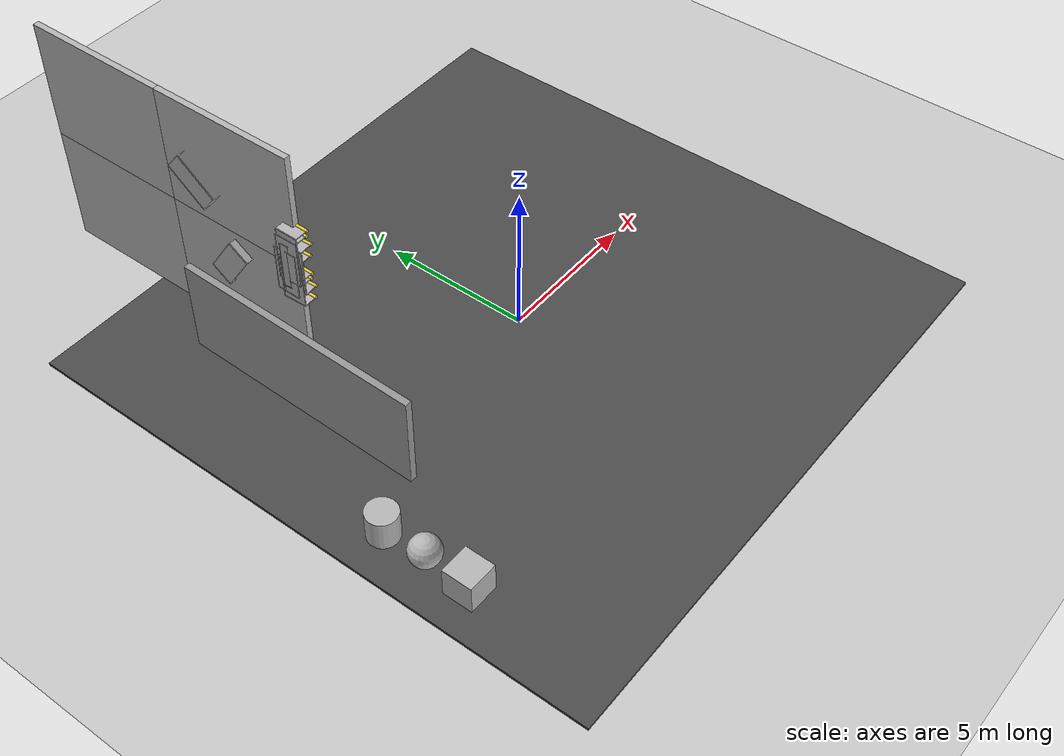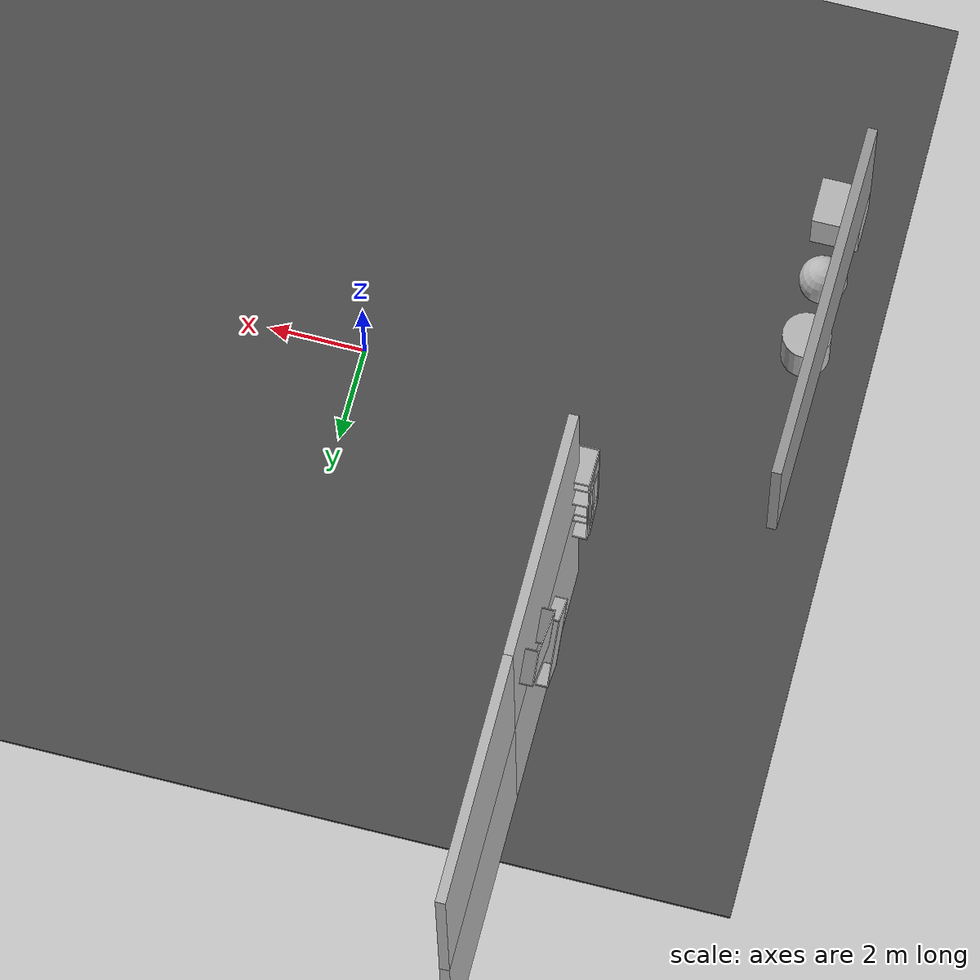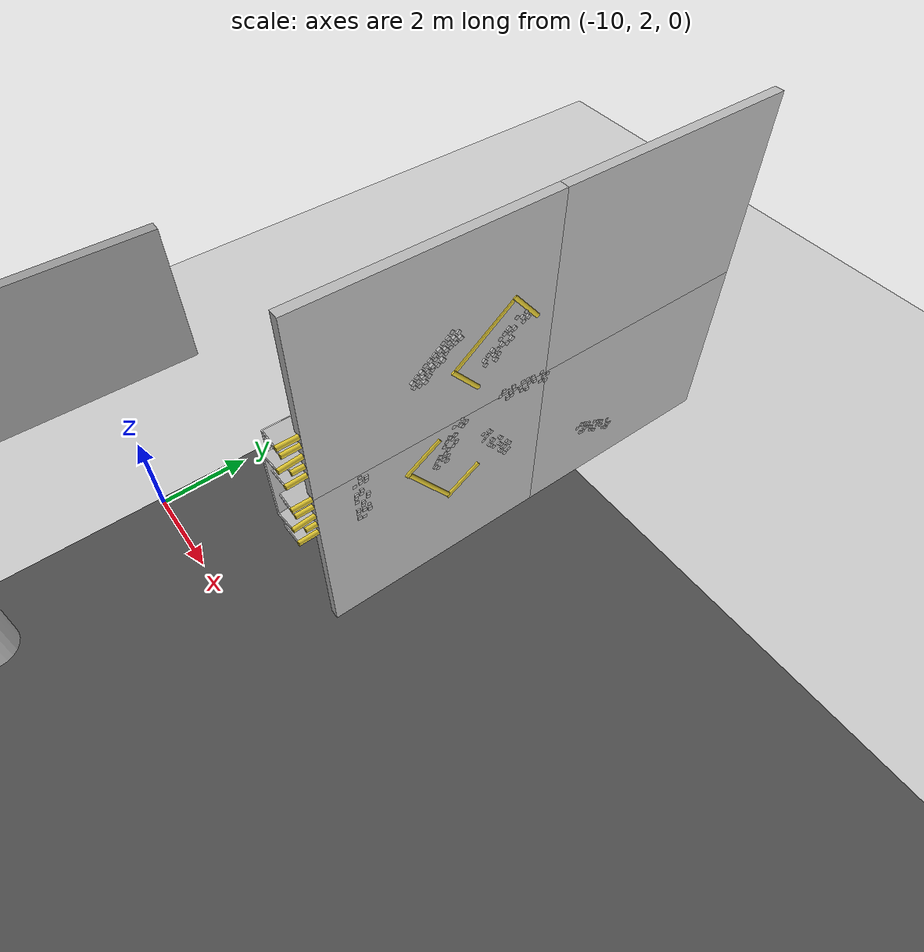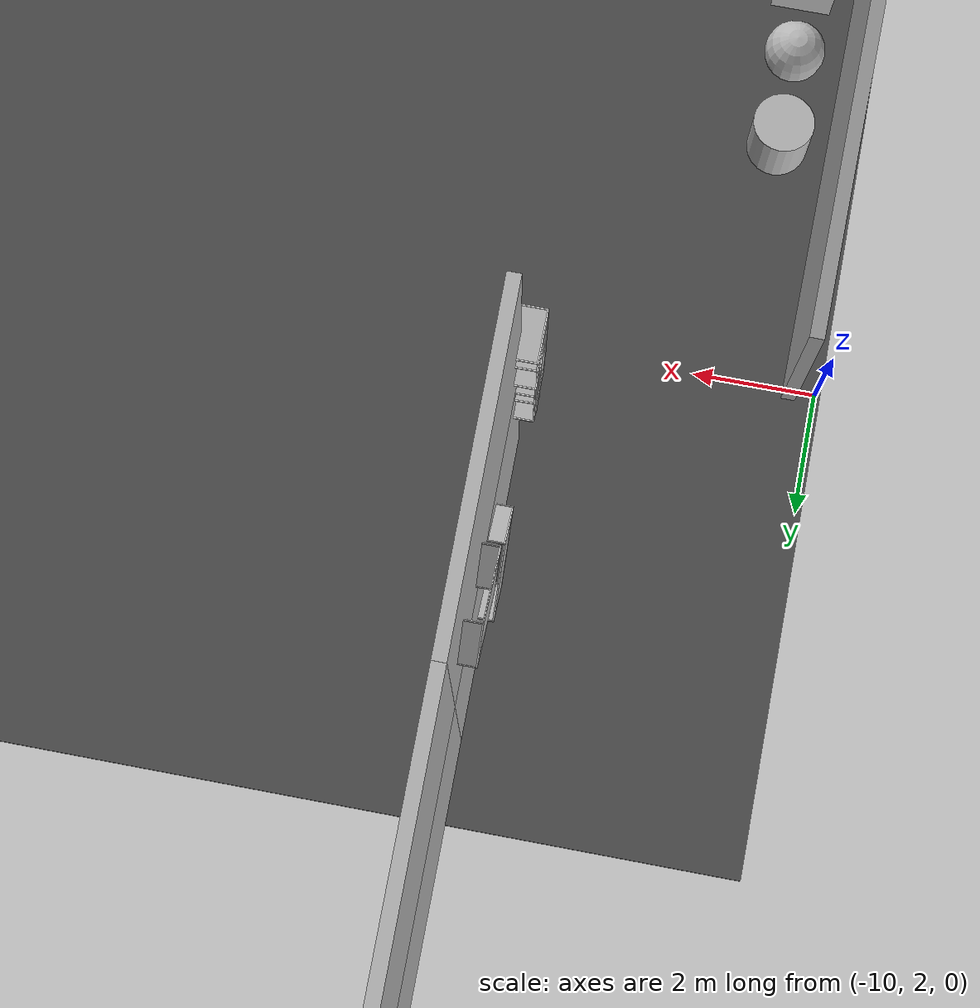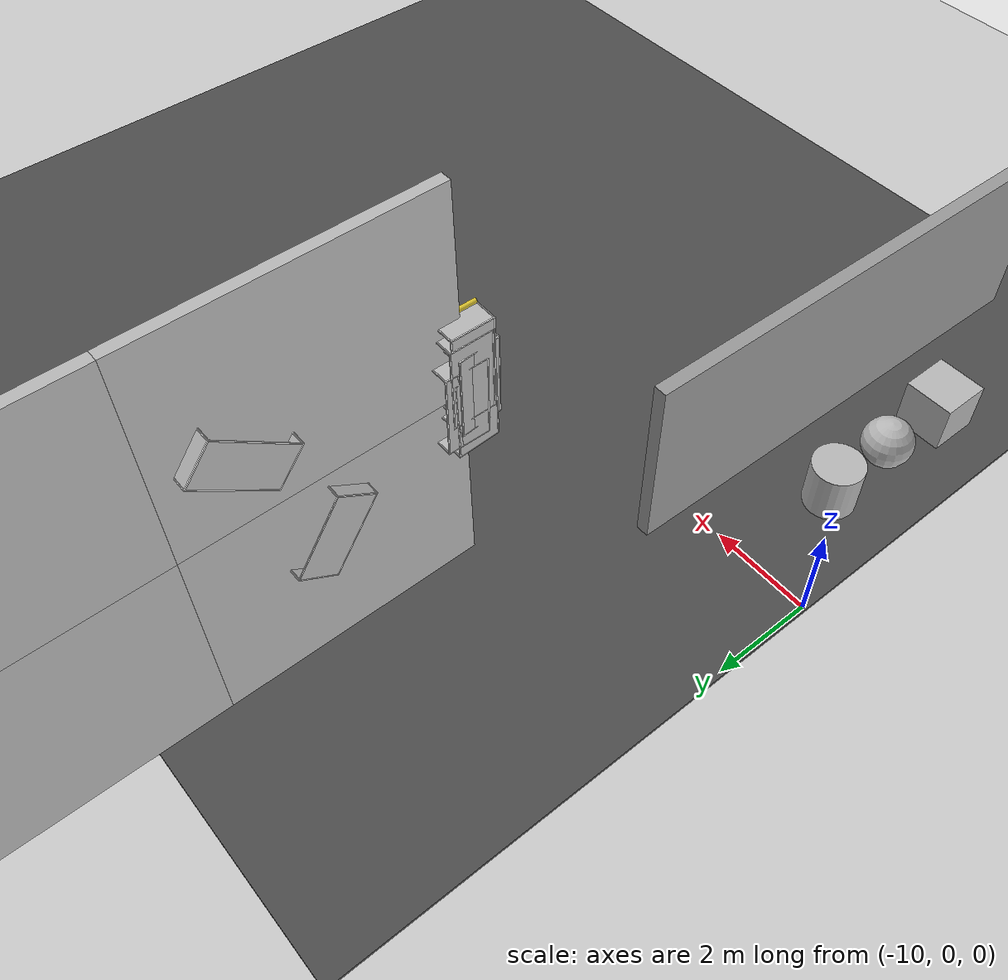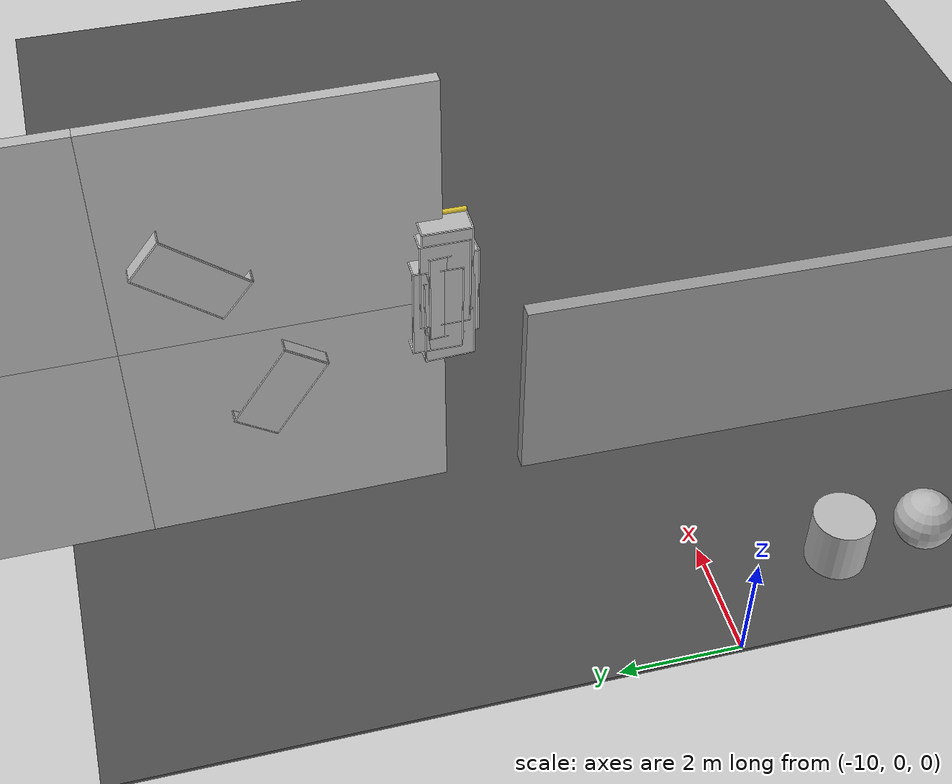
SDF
<sdf version="1.4">
 <world name="default">
  <light name="sun" type="directional">
   <pose>0 0 10 0 -0 0</pose>
   <diffuse>0.8 0.8 0.8 1</diffuse>
   <specular>0.2 0.2 0.2 1</specular>
   <attenuation>
    <range>1000</range>
    <constant>0.9</constant>
    <linear>0.01</linear>
    <quadratic>0.001</quadratic>
   </attenuation>
   <direction>-0.5 0.1 -0.9</direction>
  </light>
  <model name="ground_plane">
   <static>1</static>
   <link name="link">
    <collision name="collision">
     <geometry><plane><normal>0 0 1</normal><size>100 100</size></plane></geometry>
     <surface><friction><ode><mu>100</mu><mu2>50</mu2></ode></friction></surface>
    </collision>
    <visual name="visual">
     <cast_shadows>0</cast_shadows>
     <geometry><plane><normal>0 0 1</normal><size>100 100</size></plane></geometry>
     <material>
      <script><uri>file://media/materials/scripts/gazebo.material</uri><name>Gazebo/Grey</name></script>
     </material>
    </visual>
    <velocity_decay><linear>0</linear><angular>0</angular></velocity_decay>
   </link>
  </model>
  <physics type="ode">
   <max_step_size>0.001</max_step_size>
   <real_time_factor>1</real_time_factor>
   <real_time_update_rate>1000</real_time_update_rate>
   <gravity>0 0 -9.8</gravity>
  </physics>
  <scene><ambient>0.4 0.4 0.4 1</ambient><background>0.7 0.7 0.7 1</background><shadows>1</shadows></scene>
  <spherical_coordinates>
   <surface_model>EARTH_WGS84</surface_model>
   <latitude_deg>0</latitude_deg>
   <longitude_deg>0</longitude_deg>
   <elevation>0</elevation>
   <heading_deg>0</heading_deg>
  </spherical_coordinates>
  <model name="grey_wall">
   <static>1</static>
   <link name="link">
    <pose>0 0 1.4 0 -0 0</pose>
    <collision name="collision"><geometry><box><size>7.5 0.2 2.8</size></box></geometry></collision>
    <visual name="visual">
     <cast_shadows>0</cast_shadows>
     <geometry><box><size>7.5 0.2 2.8</size></box></geometry>
     <material>
      <script>
       <uri>model://grey_wall/materials/scripts</uri>
       <uri>model://grey_wall/materials/textures</uri>
       <name>vrc/grey_wall</name>
      </script>
     </material>
    </visual>
    <velocity_decay><linear>0</linear><angular>0</angular></velocity_decay>
   </link>
   <pose>-9.25714 -0.23164 4.42606 0 -0 1.55593</pose>
  </model>
  <model name="textured_shapes">
   <pose>-8.70069 -3.6194 0.55 0 -0 0</pose>
   <link name="box">
    <pose>0 -1.5 0 0 -0 0</pose>
    <collision name="collision"><geometry><box><size>1 1 1</size></box></geometry></collision>
    <visual name="visual">
     <geometry><box><size>1 1 1</size></box></geometry>
     <material>
      <script>
       <uri>model://textured_shapes/materials/scripts</uri>
       <uri>model://textured_shapes/materials/textures</uri>
       <name>TexturedShape/Squares</name>
      </script>
     </material>
    </visual>
    <velocity_decay><linear>0</linear><angular>0</angular></velocity_decay>
    <inertial>
     <inertia><ixx>1</ixx><ixy>0</ixy><ixz>0</ixz><iyy>1</iyy><iyz>0</iyz><izz>1</izz></inertia>
     <mass>1</mass>
    </inertial>
   </link>
   <link name="sphere">
    <collision name="collision"><geometry><sphere><radius>0.5</radius></sphere></geometry></collision>
    <visual name="visual">
     <geometry><sphere><radius>0.5</radius></sphere></geometry>
     <material>
      <script>
       <uri>model://textured_shapes/materials/scripts</uri>
       <uri>model://textured_shapes/materials/textures</uri>
       <name>TexturedShape/Squares</name>
      </script>
     </material>
    </visual>
    <velocity_decay><linear>0</linear><angular>0</angular></velocity_decay>
    <inertial>
     <inertia><ixx>1</ixx><ixy>0</ixy><ixz>0</ixz><iyy>1</iyy><iyz>0</iyz><izz>1</izz></inertia>
     <mass>1</mass>
    </inertial>
   </link>
   <link name="cylinder">
    <pose>0 1.5 0 0 -0 0</pose>
    <collision name="collision">
     <geometry><cylinder><radius>0.5</radius><length>1</length></cylinder></geometry>
    </collision>
    <visual name="visual">
     <geometry><cylinder><radius>0.5</radius><length>1</length></cylinder></geometry>
     <material>
      <script>
       <uri>model://textured_shapes/materials/scripts</uri>
       <uri>model://textured_shapes/materials/textures</uri>
       <name>TexturedShape/Squares</name>
      </script>
     </material>
    </visual>
    <velocity_decay><linear>0</linear><angular>0</angular></velocity_decay>
    <inertial>
     <inertia><ixx>1</ixx><ixy>0</ixy><ixz>0</ixz><iyy>1</iyy><iyz>0</iyz><izz>1</izz></inertia>
     <mass>1</mass>
    </inertial>
   </link>
   <static>0</static>
  </model>
  <model name="asphalt_plane_0">
   <static>1</static>
   <link name="link">
    <collision name="collision"><geometry><box><size>20 20 0.1</size></box></geometry></collision>
    <visual name="visual">
     <cast_shadows>0</cast_shadows>
     <geometry><box><size>20 20 0.1</size></box></geometry>
     <material>
      <script>
       <uri>model://asphalt_plane/materials/scripts</uri>
       <uri>model://asphalt_plane/materials/textures</uri>
       <name>vrc/asphalt</name>
      </script>
     </material>
    </visual>
    <velocity_decay><linear>0</linear><angular>0</angular></velocity_decay>
   </link>
   <pose>-0.08673 -0.042897 0 0 -0 0</pose>
  </model>
  <model name="mud_box_0">
   <static>1</static>
   <link name="link">
    <collision name="collision"><geometry><box><size>8 10 0.2</size></box></geometry></collision>
    <visual name="visual_1">
     <pose>-2 2.5 0 0 -0 0</pose>
     <cast_shadows>0</cast_shadows>
     <geometry><box><size>4 5 0.2</size></box></geometry>
     <material>
      <script>
       <uri>model://mud_box/materials/scripts</uri>
       <uri>model://mud_box/materials/textures</uri>
       <name>vrc/mud</name>
      </script>
     </material>
    </visual>
    <visual name="visual_2">
     <pose>2 2.5 0 0 -0 0</pose>
     <cast_shadows>0</cast_shadows>
     <geometry><box><size>4 5 0.2</size></box></geometry>
     <material>
      <script>
       <uri>model://mud_box/materials/scripts</uri>
       <uri>model://mud_box/materials/textures</uri>
       <name>vrc/mud</name>
      </script>
     </material>
    </visual>
    <visual name="visual_3">
     <pose>2 -2.5 0 0 -0 0</pose>
     <cast_shadows>0</cast_shadows>
     <geometry><box><size>4 5 0.2</size></box></geometry>
     <material>
      <script>
       <uri>model://mud_box/materials/scripts</uri>
       <uri>model://mud_box/materials/textures</uri>
       <name>vrc/mud</name>
      </script>
     </material>
    </visual>
    <visual name="visual_4">
     <pose>-2 -2.5 0 0 -0 0</pose>
     <cast_shadows>0</cast_shadows>
     <geometry><box><size>4 5 0.2</size></box></geometry>
     <material>
      <script>
       <uri>model://mud_box/materials/scripts</uri>
       <uri>model://mud_box/materials/textures</uri>
       <name>vrc/mud</name>
      </script>
     </material>
    </visual>
    <velocity_decay><linear>0</linear><angular>0</angular></velocity_decay>
   </link>
   <pose>-5.29758 8.63482 4.0618 0.9875 1.562 -2.15241</pose>
  </model>
  <model name="frc2016_roughterrain">
   <static>1</static>
   <link name="link">
    <visual name="platform">
     <pose>0 0 0.08269 0 -0 0</pose>
     <geometry><box><size>1.27 0.5969 0.003175</size></box></geometry>
    </visual>
    <collision name="platform">
     <pose>0 0 0.08269 0 -0 0</pose>
     <geometry><box><size>1.27 0.5969 0.003175</size></box></geometry>
    </collision>
    <visual name="row1_block1_sm">
     <pose>0.51435 0.1143 0.09698 0 -0 0</pose>
     <geometry><box><size>0.0762 0.0762 0.0254</size></box></geometry>
    </visual>
    <collision name="row1_block1_sm">
     <pose>0.51435 0.1143 0.09698 0 -0 0</pose>
     <geometry><box><size>0.0762 0.0762 0.0254</size></box></geometry>
    </collision>
    <visual name="row1_block2_lg">
     <pose>0.40005 0.1143 0.12238 0 -0 0</pose>
     <geometry><box><size>0.0762 0.0762 0.0762</size></box></geometry>
    </visual>
    <collision name="row1_block2_lg">
     <pose>0.40005 0.1143 0.12238 0 -0 0</pose>
     <geometry><box><size>0.0762 0.0762 0.0762</size></box></geometry>
    </collision>
    <visual name="row1_block3_md">
     <pose>0.28575 0.1143 0.10968 0 -0 0</pose>
     <geometry><box><size>0.0762 0.0762 0.0508</size></box></geometry>
    </visual>
    <collision name="row1_block3_md">
     <pose>0.28575 0.1143 0.10968 0 -0 0</pose>
     <geometry><box><size>0.0762 0.0762 0.0508</size></box></geometry>
    </collision>
    <visual name="row1_block4_sm">
     <pose>0.17145 0.1143 0.09698 0 -0 0</pose>
     <geometry><box><size>0.0762 0.0762 0.0254</size></box></geometry>
    </visual>
    <collision name="row1_block4_sm">
     <pose>0.17145 0.1143 0.09698 0 -0 0</pose>
     <geometry><box><size>0.0762 0.0762 0.0254</size></box></geometry>
    </collision>
    <visual name="row1_block5_md">
     <pose>0.05715 0.1143 0.10968 0 -0 0</pose>
     <geometry><box><size>0.0762 0.0762 0.0508</size></box></geometry>
    </visual>
    <collision name="row1_block5_md">
     <pose>0.05715 0.1143 0.10968 0 -0 0</pose>
     <geometry><box><size>0.0762 0.0762 0.0508</size></box></geometry>
    </collision>
    <visual name="row1_block6_lg">
     <pose>-0.05715 0.1143 0.12238 0 -0 0</pose>
     <geometry><box><size>0.0762 0.0762 0.0762</size></box></geometry>
    </visual>
    <collision name="row1_block6_lg">
     <pose>-0.05715 0.1143 0.12238 0 -0 0</pose>
     <geometry><box><size>0.0762 0.0762 0.0762</size></box></geometry>
    </collision>
    <visual name="row1_block7_sm">
     <pose>-0.17145 0.1143 0.09698 0 -0 0</pose>
     <geometry><box><size>0.0762 0.0762 0.0254</size></box></geometry>
    </visual>
    <collision name="row1_block7_sm">
     <pose>-0.17145 0.1143 0.09698 0 -0 0</pose>
     <geometry><box><size>0.0762 0.0762 0.0254</size></box></geometry>
    </collision>
    <visual name="row1_block8_sm">
     <pose>-0.28575 0.1143 0.09698 0 -0 0</pose>
     <geometry><box><size>0.0762 0.0762 0.0254</size></box></geometry>
    </visual>
    <collision name="row1_block8_sm">
     <pose>-0.28575 0.1143 0.09698 0 -0 0</pose>
     <geometry><box><size>0.0762 0.0762 0.0254</size></box></geometry>
    </collision>
    <visual name="row1_block9_md">
     <pose>-0.40005 0.1143 0.10968 0 -0 0</pose>
     <geometry><box><size>0.0762 0.0762 0.0508</size></box></geometry>
    </visual>
    <collision name="row1_block9_md">
     <pose>-0.40005 0.1143 0.10968 0 -0 0</pose>
     <geometry><box><size>0.0762 0.0762 0.0508</size></box></geometry>
    </collision>
    <visual name="row1_block10_lg">
     <pose>-0.51435 0.1143 0.12238 0 -0 0</pose>
     <geometry><box><size>0.0762 0.0762 0.0762</size></box></geometry>
    </visual>
    <collision name="row1_block10_lg">
     <pose>-0.51435 0.1143 0.12238 0 -0 0</pose>
     <geometry><box><size>0.0762 0.0762 0.0762</size></box></geometry>
    </collision>
    <visual name="row2_block1_md">
     <pose>0.5715 0 0.10968 0 -0 0</pose>
     <geometry><box><size>0.0762 0.0762 0.0508</size></box></geometry>
    </visual>
    <collision name="row2_block1_md">
     <pose>0.5715 0 0.10968 0 -0 0</pose>
     <geometry><box><size>0.0762 0.0762 0.0508</size></box></geometry>
    </collision>
    <visual name="row2_block2_sm">
     <pose>0.4572 0 0.09698 0 -0 0</pose>
     <geometry><box><size>0.0762 0.0762 0.0254</size></box></geometry>
    </visual>
    <collision name="row2_block2_sm">
     <pose>0.4572 0 0.09698 0 -0 0</pose>
     <geometry><box><size>0.0762 0.0762 0.0254</size></box></geometry>
    </collision>
    <visual name="row2_block3_lg">
     <pose>0.3429 0 0.12238 0 -0 0</pose>
     <geometry><box><size>0.0762 0.0762 0.0762</size></box></geometry>
    </visual>
    <collision name="row2_block3_lg">
     <pose>0.3429 0 0.12238 0 -0 0</pose>
     <geometry><box><size>0.0762 0.0762 0.0762</size></box></geometry>
    </collision>
    <visual name="row2_block4_md">
     <pose>0.2286 0 0.10968 0 -0 0</pose>
     <geometry><box><size>0.0762 0.0762 0.0508</size></box></geometry>
    </visual>
    <collision name="row2_block4_md">
     <pose>0.2286 0 0.10968 0 -0 0</pose>
     <geometry><box><size>0.0762 0.0762 0.0508</size></box></geometry>
    </collision>
    <visual name="row2_block5_lg">
     <pose>0.1143 0 0.12238 0 -0 0</pose>
     <geometry><box><size>0.0762 0.0762 0.0762</size></box></geometry>
    </visual>
    <collision name="row2_block5_lg">
     <pose>0.1143 0 0.12238 0 -0 0</pose>
     <geometry><box><size>0.0762 0.0762 0.0762</size></box></geometry>
    </collision>
    <visual name="row2_block6_sm">
     <pose>0 0 0.09698 0 -0 0</pose>
     <geometry><box><size>0.0762 0.0762 0.0254</size></box></geometry>
    </visual>
    <collision name="row2_block6_sm">
     <pose>0 0 0.09698 0 -0 0</pose>
     <geometry><box><size>0.0762 0.0762 0.0254</size></box></geometry>
    </collision>
    <visual name="row2_block7_md">
     <pose>-0.1143 0 0.10968 0 -0 0</pose>
     <geometry><box><size>0.0762 0.0762 0.0508</size></box></geometry>
    </visual>
    <collision name="row2_block7_md">
     <pose>-0.1143 0 0.10968 0 -0 0</pose>
     <geometry><box><size>0.0762 0.0762 0.0508</size></box></geometry>
    </collision>
    <visual name="row2_block8_lg">
     <pose>-0.2286 0 0.12238 0 -0 0</pose>
     <geometry><box><size>0.0762 0.0762 0.0762</size></box></geometry>
    </visual>
    <collision name="row2_block8_lg">
     <pose>-0.2286 0 0.12238 0 -0 0</pose>
     <geometry><box><size>0.0762 0.0762 0.0762</size></box></geometry>
    </collision>
    <visual name="row2_block9_sm">
     <pose>-0.3429 0 0.09698 0 -0 0</pose>
     <geometry><box><size>0.0762 0.0762 0.0254</size></box></geometry>
    </visual>
    <collision name="row2_block9_sm">
     <pose>-0.3429 0 0.09698 0 -0 0</pose>
     <geometry><box><size>0.0762 0.0762 0.0254</size></box></geometry>
    </collision>
    <visual name="row2_block10_lg">
     <pose>-0.4572 0 0.12238 0 -0 0</pose>
     <geometry><box><size>0.0762 0.0762 0.0762</size></box></geometry>
    </visual>
    <collision name="row2_block10_lg">
     <pose>-0.4572 0 0.12238 0 -0 0</pose>
     <geometry><box><size>0.0762 0.0762 0.0762</size></box></geometry>
    </collision>
    <visual name="row2_block11_md">
     <pose>-0.5715 0 0.10968 0 -0 0</pose>
     <geometry><box><size>0.0762 0.0762 0.0508</size></box></geometry>
    </visual>
    <collision name="row2_block11_md">
     <pose>-0.5715 0 0.10968 0 -0 0</pose>
     <geometry><box><size>0.0762 0.0762 0.0508</size></box></geometry>
    </collision>
    <visual name="row3_block1_lg">
     <pose>0.51435 -0.1143 0.12238 0 -0 0</pose>
     <geometry><box><size>0.0762 0.0762 0.0762</size></box></geometry>
    </visual>
    <collision name="row3_block1_lg">
     <pose>0.51435 -0.1143 0.12238 0 -0 0</pose>
     <geometry><box><size>0.0762 0.0762 0.0762</size></box></geometry>
    </collision>
    <visual name="row3_block2_md">
     <pose>0.40005 -0.1143 0.10968 0 -0 0</pose>
     <geometry><box><size>0.0762 0.0762 0.0508</size></box></geometry>
    </visual>
    <collision name="row3_block2_md">
     <pose>0.40005 -0.1143 0.10968 0 -0 0</pose>
     <geometry><box><size>0.0762 0.0762 0.0508</size></box></geometry>
    </collision>
    <visual name="row3_block3_lg">
     <pose>0.28575 -0.1143 0.12238 0 -0 0</pose>
     <geometry><box><size>0.0762 0.0762 0.0762</size></box></geometry>
    </visual>
    <collision name="row3_block3_lg">
     <pose>0.28575 -0.1143 0.12238 0 -0 0</pose>
     <geometry><box><size>0.0762 0.0762 0.0762</size></box></geometry>
    </collision>
    <visual name="row3_block4_sm">
     <pose>0.17145 -0.1143 0.09698 0 -0 0</pose>
     <geometry><box><size>0.0762 0.0762 0.0254</size></box></geometry>
    </visual>
    <collision name="row3_block4_sm">
     <pose>0.17145 -0.1143 0.09698 0 -0 0</pose>
     <geometry><box><size>0.0762 0.0762 0.0254</size></box></geometry>
    </collision>
    <visual name="row3_block5_md">
     <pose>0.05715 -0.1143 0.10968 0 -0 0</pose>
     <geometry><box><size>0.0762 0.0762 0.0508</size></box></geometry>
    </visual>
    <collision name="row3_block5_md">
     <pose>0.05715 -0.1143 0.10968 0 -0 0</pose>
     <geometry><box><size>0.0762 0.0762 0.0508</size></box></geometry>
    </collision>
    <visual name="row3_block6_md">
     <pose>-0.05715 -0.1143 0.10968 0 -0 0</pose>
     <geometry><box><size>0.0762 0.0762 0.0508</size></box></geometry>
    </visual>
    <collision name="row3_block6_md">
     <pose>-0.05715 -0.1143 0.10968 0 -0 0</pose>
     <geometry><box><size>0.0762 0.0762 0.0508</size></box></geometry>
    </collision>
    <visual name="row3_block7_lg">
     <pose>-0.17145 -0.1143 0.12238 0 -0 0</pose>
     <geometry><box><size>0.0762 0.0762 0.0762</size></box></geometry>
    </visual>
    <collision name="row3_block7_lg">
     <pose>-0.17145 -0.1143 0.12238 0 -0 0</pose>
     <geometry><box><size>0.0762 0.0762 0.0762</size></box></geometry>
    </collision>
    <visual name="row3_block8_sm">
     <pose>-0.28575 -0.1143 0.09698 0 -0 0</pose>
     <geometry><box><size>0.0762 0.0762 0.0254</size></box></geometry>
    </visual>
    <collision name="row3_block8_sm">
     <pose>-0.28575 -0.1143 0.09698 0 -0 0</pose>
     <geometry><box><size>0.0762 0.0762 0.0254</size></box></geometry>
    </collision>
    <visual name="row3_block9_md">
     <pose>-0.40005 -0.1143 0.10968 0 -0 0</pose>
     <geometry><box><size>0.0762 0.0762 0.0508</size></box></geometry>
    </visual>
    <collision name="row3_block9_md">
     <pose>-0.40005 -0.1143 0.10968 0 -0 0</pose>
     <geometry><box><size>0.0762 0.0762 0.0508</size></box></geometry>
    </collision>
    <visual name="row3_block10_sm">
     <pose>-0.51435 -0.1143 0.09698 0 -0 0</pose>
     <geometry><box><size>0.0762 0.0762 0.0254</size></box></geometry>
    </visual>
    <collision name="row3_block10_sm">
     <pose>-0.51435 -0.1143 0.09698 0 -0 0</pose>
     <geometry><box><size>0.0762 0.0762 0.0254</size></box></geometry>
    </collision>
    <velocity_decay><linear>0</linear><angular>0</angular></velocity_decay>
   </link>
   <pose>-5.32658 6.41708 3.55024 -1.57835 1.07404 -1.57744</pose>
  </model>
  <model name="frc2016_roughterrain_0">
   <static>1</static>
   <link name="link">
    <visual name="platform">
     <pose>0 0 0.08269 0 -0 0</pose>
     <geometry><box><size>1.27 0.5969 0.003175</size></box></geometry>
    </visual>
    <collision name="platform">
     <pose>0 0 0.08269 0 -0 0</pose>
     <geometry><box><size>1.27 0.5969 0.003175</size></box></geometry>
    </collision>
    <visual name="row1_block1_sm">
     <pose>0.51435 0.1143 0.09698 0 -0 0</pose>
     <geometry><box><size>0.0762 0.0762 0.0254</size></box></geometry>
    </visual>
    <collision name="row1_block1_sm">
     <pose>0.51435 0.1143 0.09698 0 -0 0</pose>
     <geometry><box><size>0.0762 0.0762 0.0254</size></box></geometry>
    </collision>
    <visual name="row1_block2_lg">
     <pose>0.40005 0.1143 0.12238 0 -0 0</pose>
     <geometry><box><size>0.0762 0.0762 0.0762</size></box></geometry>
    </visual>
    <collision name="row1_block2_lg">
     <pose>0.40005 0.1143 0.12238 0 -0 0</pose>
     <geometry><box><size>0.0762 0.0762 0.0762</size></box></geometry>
    </collision>
    <visual name="row1_block3_md">
     <pose>0.28575 0.1143 0.10968 0 -0 0</pose>
     <geometry><box><size>0.0762 0.0762 0.0508</size></box></geometry>
    </visual>
    <collision name="row1_block3_md">
     <pose>0.28575 0.1143 0.10968 0 -0 0</pose>
     <geometry><box><size>0.0762 0.0762 0.0508</size></box></geometry>
    </collision>
    <visual name="row1_block4_sm">
     <pose>0.17145 0.1143 0.09698 0 -0 0</pose>
     <geometry><box><size>0.0762 0.0762 0.0254</size></box></geometry>
    </visual>
    <collision name="row1_block4_sm">
     <pose>0.17145 0.1143 0.09698 0 -0 0</pose>
     <geometry><box><size>0.0762 0.0762 0.0254</size></box></geometry>
    </collision>
    <visual name="row1_block5_md">
     <pose>0.05715 0.1143 0.10968 0 -0 0</pose>
     <geometry><box><size>0.0762 0.0762 0.0508</size></box></geometry>
    </visual>
    <collision name="row1_block5_md">
     <pose>0.05715 0.1143 0.10968 0 -0 0</pose>
     <geometry><box><size>0.0762 0.0762 0.0508</size></box></geometry>
    </collision>
    <visual name="row1_block6_lg">
     <pose>-0.05715 0.1143 0.12238 0 -0 0</pose>
     <geometry><box><size>0.0762 0.0762 0.0762</size></box></geometry>
    </visual>
    <collision name="row1_block6_lg">
     <pose>-0.05715 0.1143 0.12238 0 -0 0</pose>
     <geometry><box><size>0.0762 0.0762 0.0762</size></box></geometry>
    </collision>
    <visual name="row1_block7_sm">
     <pose>-0.17145 0.1143 0.09698 0 -0 0</pose>
     <geometry><box><size>0.0762 0.0762 0.0254</size></box></geometry>
    </visual>
    <collision name="row1_block7_sm">
     <pose>-0.17145 0.1143 0.09698 0 -0 0</pose>
     <geometry><box><size>0.0762 0.0762 0.0254</size></box></geometry>
    </collision>
    <visual name="row1_block8_sm">
     <pose>-0.28575 0.1143 0.09698 0 -0 0</pose>
     <geometry><box><size>0.0762 0.0762 0.0254</size></box></geometry>
    </visual>
    <collision name="row1_block8_sm">
     <pose>-0.28575 0.1143 0.09698 0 -0 0</pose>
     <geometry><box><size>0.0762 0.0762 0.0254</size></box></geometry>
    </collision>
    <visual name="row1_block9_md">
     <pose>-0.40005 0.1143 0.10968 0 -0 0</pose>
     <geometry><box><size>0.0762 0.0762 0.0508</size></box></geometry>
    </visual>
    <collision name="row1_block9_md">
     <pose>-0.40005 0.1143 0.10968 0 -0 0</pose>
     <geometry><box><size>0.0762 0.0762 0.0508</size></box></geometry>
    </collision>
    <visual name="row1_block10_lg">
     <pose>-0.51435 0.1143 0.12238 0 -0 0</pose>
     <geometry><box><size>0.0762 0.0762 0.0762</size></box></geometry>
    </visual>
    <collision name="row1_block10_lg">
     <pose>-0.51435 0.1143 0.12238 0 -0 0</pose>
     <geometry><box><size>0.0762 0.0762 0.0762</size></box></geometry>
    </collision>
    <visual name="row2_block1_md">
     <pose>0.5715 0 0.10968 0 -0 0</pose>
     <geometry><box><size>0.0762 0.0762 0.0508</size></box></geometry>
    </visual>
    <collision name="row2_block1_md">
     <pose>0.5715 0 0.10968 0 -0 0</pose>
     <geometry><box><size>0.0762 0.0762 0.0508</size></box></geometry>
    </collision>
    <visual name="row2_block2_sm">
     <pose>0.4572 0 0.09698 0 -0 0</pose>
     <geometry><box><size>0.0762 0.0762 0.0254</size></box></geometry>
    </visual>
    <collision name="row2_block2_sm">
     <pose>0.4572 0 0.09698 0 -0 0</pose>
     <geometry><box><size>0.0762 0.0762 0.0254</size></box></geometry>
    </collision>
    <visual name="row2_block3_lg">
     <pose>0.3429 0 0.12238 0 -0 0</pose>
     <geometry><box><size>0.0762 0.0762 0.0762</size></box></geometry>
    </visual>
    <collision name="row2_block3_lg">
     <pose>0.3429 0 0.12238 0 -0 0</pose>
     <geometry><box><size>0.0762 0.0762 0.0762</size></box></geometry>
    </collision>
    <visual name="row2_block4_md">
     <pose>0.2286 0 0.10968 0 -0 0</pose>
     <geometry><box><size>0.0762 0.0762 0.0508</size></box></geometry>
    </visual>
    <collision name="row2_block4_md">
     <pose>0.2286 0 0.10968 0 -0 0</pose>
     <geometry><box><size>0.0762 0.0762 0.0508</size></box></geometry>
    </collision>
    <visual name="row2_block5_lg">
     <pose>0.1143 0 0.12238 0 -0 0</pose>
     <geometry><box><size>0.0762 0.0762 0.0762</size></box></geometry>
    </visual>
    <collision name="row2_block5_lg">
     <pose>0.1143 0 0.12238 0 -0 0</pose>
     <geometry><box><size>0.0762 0.0762 0.0762</size></box></geometry>
    </collision>
    <visual name="row2_block6_sm">
     <pose>0 0 0.09698 0 -0 0</pose>
     <geometry><box><size>0.0762 0.0762 0.0254</size></box></geometry>
    </visual>
    <collision name="row2_block6_sm">
     <pose>0 0 0.09698 0 -0 0</pose>
     <geometry><box><size>0.0762 0.0762 0.0254</size></box></geometry>
    </collision>
    <visual name="row2_block7_md">
     <pose>-0.1143 0 0.10968 0 -0 0</pose>
     <geometry><box><size>0.0762 0.0762 0.0508</size></box></geometry>
    </visual>
    <collision name="row2_block7_md">
     <pose>-0.1143 0 0.10968 0 -0 0</pose>
     <geometry><box><size>0.0762 0.0762 0.0508</size></box></geometry>
    </collision>
    <visual name="row2_block8_lg">
     <pose>-0.2286 0 0.12238 0 -0 0</pose>
     <geometry><box><size>0.0762 0.0762 0.0762</size></box></geometry>
    </visual>
    <collision name="row2_block8_lg">
     <pose>-0.2286 0 0.12238 0 -0 0</pose>
     <geometry><box><size>0.0762 0.0762 0.0762</size></box></geometry>
    </collision>
    <visual name="row2_block9_sm">
     <pose>-0.3429 0 0.09698 0 -0 0</pose>
     <geometry><box><size>0.0762 0.0762 0.0254</size></box></geometry>
    </visual>
    <collision name="row2_block9_sm">
     <pose>-0.3429 0 0.09698 0 -0 0</pose>
     <geometry><box><size>0.0762 0.0762 0.0254</size></box></geometry>
    </collision>
    <visual name="row2_block10_lg">
     <pose>-0.4572 0 0.12238 0 -0 0</pose>
     <geometry><box><size>0.0762 0.0762 0.0762</size></box></geometry>
    </visual>
    <collision name="row2_block10_lg">
     <pose>-0.4572 0 0.12238 0 -0 0</pose>
     <geometry><box><size>0.0762 0.0762 0.0762</size></box></geometry>
    </collision>
    <visual name="row2_block11_md">
     <pose>-0.5715 0 0.10968 0 -0 0</pose>
     <geometry><box><size>0.0762 0.0762 0.0508</size></box></geometry>
    </visual>
    <collision name="row2_block11_md">
     <pose>-0.5715 0 0.10968 0 -0 0</pose>
     <geometry><box><size>0.0762 0.0762 0.0508</size></box></geometry>
    </collision>
    <visual name="row3_block1_lg">
     <pose>0.51435 -0.1143 0.12238 0 -0 0</pose>
     <geometry><box><size>0.0762 0.0762 0.0762</size></box></geometry>
    </visual>
    <collision name="row3_block1_lg">
     <pose>0.51435 -0.1143 0.12238 0 -0 0</pose>
     <geometry><box><size>0.0762 0.0762 0.0762</size></box></geometry>
    </collision>
    <visual name="row3_block2_md">
     <pose>0.40005 -0.1143 0.10968 0 -0 0</pose>
     <geometry><box><size>0.0762 0.0762 0.0508</size></box></geometry>
    </visual>
    <collision name="row3_block2_md">
     <pose>0.40005 -0.1143 0.10968 0 -0 0</pose>
     <geometry><box><size>0.0762 0.0762 0.0508</size></box></geometry>
    </collision>
    <visual name="row3_block3_lg">
     <pose>0.28575 -0.1143 0.12238 0 -0 0</pose>
     <geometry><box><size>0.0762 0.0762 0.0762</size></box></geometry>
    </visual>
    <collision name="row3_block3_lg">
     <pose>0.28575 -0.1143 0.12238 0 -0 0</pose>
     <geometry><box><size>0.0762 0.0762 0.0762</size></box></geometry>
    </collision>
    <visual name="row3_block4_sm">
     <pose>0.17145 -0.1143 0.09698 0 -0 0</pose>
     <geometry><box><size>0.0762 0.0762 0.0254</size></box></geometry>
    </visual>
    <collision name="row3_block4_sm">
     <pose>0.17145 -0.1143 0.09698 0 -0 0</pose>
     <geometry><box><size>0.0762 0.0762 0.0254</size></box></geometry>
    </collision>
    <visual name="row3_block5_md">
     <pose>0.05715 -0.1143 0.10968 0 -0 0</pose>
     <geometry><box><size>0.0762 0.0762 0.0508</size></box></geometry>
    </visual>
    <collision name="row3_block5_md">
     <pose>0.05715 -0.1143 0.10968 0 -0 0</pose>
     <geometry><box><size>0.0762 0.0762 0.0508</size></box></geometry>
    </collision>
    <visual name="row3_block6_md">
     <pose>-0.05715 -0.1143 0.10968 0 -0 0</pose>
     <geometry><box><size>0.0762 0.0762 0.0508</size></box></geometry>
    </visual>
    <collision name="row3_block6_md">
     <pose>-0.05715 -0.1143 0.10968 0 -0 0</pose>
     <geometry><box><size>0.0762 0.0762 0.0508</size></box></geometry>
    </collision>
    <visual name="row3_block7_lg">
     <pose>-0.17145 -0.1143 0.12238 0 -0 0</pose>
     <geometry><box><size>0.0762 0.0762 0.0762</size></box></geometry>
    </visual>
    <collision name="row3_block7_lg">
     <pose>-0.17145 -0.1143 0.12238 0 -0 0</pose>
     <geometry><box><size>0.0762 0.0762 0.0762</size></box></geometry>
    </collision>
    <visual name="row3_block8_sm">
     <pose>-0.28575 -0.1143 0.09698 0 -0 0</pose>
     <geometry><box><size>0.0762 0.0762 0.0254</size></box></geometry>
    </visual>
    <collision name="row3_block8_sm">
     <pose>-0.28575 -0.1143 0.09698 0 -0 0</pose>
     <geometry><box><size>0.0762 0.0762 0.0254</size></box></geometry>
    </collision>
    <visual name="row3_block9_md">
     <pose>-0.40005 -0.1143 0.10968 0 -0 0</pose>
     <geometry><box><size>0.0762 0.0762 0.0508</size></box></geometry>
    </visual>
    <collision name="row3_block9_md">
     <pose>-0.40005 -0.1143 0.10968 0 -0 0</pose>
     <geometry><box><size>0.0762 0.0762 0.0508</size></box></geometry>
    </collision>
    <visual name="row3_block10_sm">
     <pose>-0.51435 -0.1143 0.09698 0 -0 0</pose>
     <geometry><box><size>0.0762 0.0762 0.0254</size></box></geometry>
    </visual>
    <collision name="row3_block10_sm">
     <pose>-0.51435 -0.1143 0.09698 0 -0 0</pose>
     <geometry><box><size>0.0762 0.0762 0.0254</size></box></geometry>
    </collision>
    <velocity_decay><linear>0</linear><angular>0</angular></velocity_decay>
   </link>
   <pose>-5.34331 10.3016 1.37254 -1.59145 -0.468069 -1.56148</pose>
  </model>
  <model name="frc2016_roughterrain_1">
   <static>1</static>
   <link name="link">
    <visual name="platform">
     <pose>0 0 0.08269 0 -0 0</pose>
     <geometry><box><size>1.27 0.5969 0.003175</size></box></geometry>
    </visual>
    <collision name="platform">
     <pose>0 0 0.08269 0 -0 0</pose>
     <geometry><box><size>1.27 0.5969 0.003175</size></box></geometry>
    </collision>
    <visual name="row1_block1_sm">
     <pose>0.51435 0.1143 0.09698 0 -0 0</pose>
     <geometry><box><size>0.0762 0.0762 0.0254</size></box></geometry>
    </visual>
    <collision name="row1_block1_sm">
     <pose>0.51435 0.1143 0.09698 0 -0 0</pose>
     <geometry><box><size>0.0762 0.0762 0.0254</size></box></geometry>
    </collision>
    <visual name="row1_block2_lg">
     <pose>0.40005 0.1143 0.12238 0 -0 0</pose>
     <geometry><box><size>0.0762 0.0762 0.0762</size></box></geometry>
    </visual>
    <collision name="row1_block2_lg">
     <pose>0.40005 0.1143 0.12238 0 -0 0</pose>
     <geometry><box><size>0.0762 0.0762 0.0762</size></box></geometry>
    </collision>
    <visual name="row1_block3_md">
     <pose>0.28575 0.1143 0.10968 0 -0 0</pose>
     <geometry><box><size>0.0762 0.0762 0.0508</size></box></geometry>
    </visual>
    <collision name="row1_block3_md">
     <pose>0.28575 0.1143 0.10968 0 -0 0</pose>
     <geometry><box><size>0.0762 0.0762 0.0508</size></box></geometry>
    </collision>
    <visual name="row1_block4_sm">
     <pose>0.17145 0.1143 0.09698 0 -0 0</pose>
     <geometry><box><size>0.0762 0.0762 0.0254</size></box></geometry>
    </visual>
    <collision name="row1_block4_sm">
     <pose>0.17145 0.1143 0.09698 0 -0 0</pose>
     <geometry><box><size>0.0762 0.0762 0.0254</size></box></geometry>
    </collision>
    <visual name="row1_block5_md">
     <pose>0.05715 0.1143 0.10968 0 -0 0</pose>
     <geometry><box><size>0.0762 0.0762 0.0508</size></box></geometry>
    </visual>
    <collision name="row1_block5_md">
     <pose>0.05715 0.1143 0.10968 0 -0 0</pose>
     <geometry><box><size>0.0762 0.0762 0.0508</size></box></geometry>
    </collision>
    <visual name="row1_block6_lg">
     <pose>-0.05715 0.1143 0.12238 0 -0 0</pose>
     <geometry><box><size>0.0762 0.0762 0.0762</size></box></geometry>
    </visual>
    <collision name="row1_block6_lg">
     <pose>-0.05715 0.1143 0.12238 0 -0 0</pose>
     <geometry><box><size>0.0762 0.0762 0.0762</size></box></geometry>
    </collision>
    <visual name="row1_block7_sm">
     <pose>-0.17145 0.1143 0.09698 0 -0 0</pose>
     <geometry><box><size>0.0762 0.0762 0.0254</size></box></geometry>
    </visual>
    <collision name="row1_block7_sm">
     <pose>-0.17145 0.1143 0.09698 0 -0 0</pose>
     <geometry><box><size>0.0762 0.0762 0.0254</size></box></geometry>
    </collision>
    <visual name="row1_block8_sm">
     <pose>-0.28575 0.1143 0.09698 0 -0 0</pose>
     <geometry><box><size>0.0762 0.0762 0.0254</size></box></geometry>
    </visual>
    <collision name="row1_block8_sm">
     <pose>-0.28575 0.1143 0.09698 0 -0 0</pose>
     <geometry><box><size>0.0762 0.0762 0.0254</size></box></geometry>
    </collision>
    <visual name="row1_block9_md">
     <pose>-0.40005 0.1143 0.10968 0 -0 0</pose>
     <geometry><box><size>0.0762 0.0762 0.0508</size></box></geometry>
    </visual>
    <collision name="row1_block9_md">
     <pose>-0.40005 0.1143 0.10968 0 -0 0</pose>
     <geometry><box><size>0.0762 0.0762 0.0508</size></box></geometry>
    </collision>
    <visual name="row1_block10_lg">
     <pose>-0.51435 0.1143 0.12238 0 -0 0</pose>
     <geometry><box><size>0.0762 0.0762 0.0762</size></box></geometry>
    </visual>
    <collision name="row1_block10_lg">
     <pose>-0.51435 0.1143 0.12238 0 -0 0</pose>
     <geometry><box><size>0.0762 0.0762 0.0762</size></box></geometry>
    </collision>
    <visual name="row2_block1_md">
     <pose>0.5715 0 0.10968 0 -0 0</pose>
     <geometry><box><size>0.0762 0.0762 0.0508</size></box></geometry>
    </visual>
    <collision name="row2_block1_md">
     <pose>0.5715 0 0.10968 0 -0 0</pose>
     <geometry><box><size>0.0762 0.0762 0.0508</size></box></geometry>
    </collision>
    <visual name="row2_block2_sm">
     <pose>0.4572 0 0.09698 0 -0 0</pose>
     <geometry><box><size>0.0762 0.0762 0.0254</size></box></geometry>
    </visual>
    <collision name="row2_block2_sm">
     <pose>0.4572 0 0.09698 0 -0 0</pose>
     <geometry><box><size>0.0762 0.0762 0.0254</size></box></geometry>
    </collision>
    <visual name="row2_block3_lg">
     <pose>0.3429 0 0.12238 0 -0 0</pose>
     <geometry><box><size>0.0762 0.0762 0.0762</size></box></geometry>
    </visual>
    <collision name="row2_block3_lg">
     <pose>0.3429 0 0.12238 0 -0 0</pose>
     <geometry><box><size>0.0762 0.0762 0.0762</size></box></geometry>
    </collision>
    <visual name="row2_block4_md">
     <pose>0.2286 0 0.10968 0 -0 0</pose>
     <geometry><box><size>0.0762 0.0762 0.0508</size></box></geometry>
    </visual>
    <collision name="row2_block4_md">
     <pose>0.2286 0 0.10968 0 -0 0</pose>
     <geometry><box><size>0.0762 0.0762 0.0508</size></box></geometry>
    </collision>
    <visual name="row2_block5_lg">
     <pose>0.1143 0 0.12238 0 -0 0</pose>
     <geometry><box><size>0.0762 0.0762 0.0762</size></box></geometry>
    </visual>
    <collision name="row2_block5_lg">
     <pose>0.1143 0 0.12238 0 -0 0</pose>
     <geometry><box><size>0.0762 0.0762 0.0762</size></box></geometry>
    </collision>
    <visual name="row2_block6_sm">
     <pose>0 0 0.09698 0 -0 0</pose>
     <geometry><box><size>0.0762 0.0762 0.0254</size></box></geometry>
    </visual>
    <collision name="row2_block6_sm">
     <pose>0 0 0.09698 0 -0 0</pose>
     <geometry><box><size>0.0762 0.0762 0.0254</size></box></geometry>
    </collision>
    <visual name="row2_block7_md">
     <pose>-0.1143 0 0.10968 0 -0 0</pose>
     <geometry><box><size>0.0762 0.0762 0.0508</size></box></geometry>
    </visual>
    <collision name="row2_block7_md">
     <pose>-0.1143 0 0.10968 0 -0 0</pose>
     <geometry><box><size>0.0762 0.0762 0.0508</size></box></geometry>
    </collision>
    <visual name="row2_block8_lg">
     <pose>-0.2286 0 0.12238 0 -0 0</pose>
     <geometry><box><size>0.0762 0.0762 0.0762</size></box></geometry>
    </visual>
    <collision name="row2_block8_lg">
     <pose>-0.2286 0 0.12238 0 -0 0</pose>
     <geometry><box><size>0.0762 0.0762 0.0762</size></box></geometry>
    </collision>
    <visual name="row2_block9_sm">
     <pose>-0.3429 0 0.09698 0 -0 0</pose>
     <geometry><box><size>0.0762 0.0762 0.0254</size></box></geometry>
    </visual>
    <collision name="row2_block9_sm">
     <pose>-0.3429 0 0.09698 0 -0 0</pose>
     <geometry><box><size>0.0762 0.0762 0.0254</size></box></geometry>
    </collision>
    <visual name="row2_block10_lg">
     <pose>-0.4572 0 0.12238 0 -0 0</pose>
     <geometry><box><size>0.0762 0.0762 0.0762</size></box></geometry>
    </visual>
    <collision name="row2_block10_lg">
     <pose>-0.4572 0 0.12238 0 -0 0</pose>
     <geometry><box><size>0.0762 0.0762 0.0762</size></box></geometry>
    </collision>
    <visual name="row2_block11_md">
     <pose>-0.5715 0 0.10968 0 -0 0</pose>
     <geometry><box><size>0.0762 0.0762 0.0508</size></box></geometry>
    </visual>
    <collision name="row2_block11_md">
     <pose>-0.5715 0 0.10968 0 -0 0</pose>
     <geometry><box><size>0.0762 0.0762 0.0508</size></box></geometry>
    </collision>
    <visual name="row3_block1_lg">
     <pose>0.51435 -0.1143 0.12238 0 -0 0</pose>
     <geometry><box><size>0.0762 0.0762 0.0762</size></box></geometry>
    </visual>
    <collision name="row3_block1_lg">
     <pose>0.51435 -0.1143 0.12238 0 -0 0</pose>
     <geometry><box><size>0.0762 0.0762 0.0762</size></box></geometry>
    </collision>
    <visual name="row3_block2_md">
     <pose>0.40005 -0.1143 0.10968 0 -0 0</pose>
     <geometry><box><size>0.0762 0.0762 0.0508</size></box></geometry>
    </visual>
    <collision name="row3_block2_md">
     <pose>0.40005 -0.1143 0.10968 0 -0 0</pose>
     <geometry><box><size>0.0762 0.0762 0.0508</size></box></geometry>
    </collision>
    <visual name="row3_block3_lg">
     <pose>0.28575 -0.1143 0.12238 0 -0 0</pose>
     <geometry><box><size>0.0762 0.0762 0.0762</size></box></geometry>
    </visual>
    <collision name="row3_block3_lg">
     <pose>0.28575 -0.1143 0.12238 0 -0 0</pose>
     <geometry><box><size>0.0762 0.0762 0.0762</size></box></geometry>
    </collision>
    <visual name="row3_block4_sm">
     <pose>0.17145 -0.1143 0.09698 0 -0 0</pose>
     <geometry><box><size>0.0762 0.0762 0.0254</size></box></geometry>
    </visual>
    <collision name="row3_block4_sm">
     <pose>0.17145 -0.1143 0.09698 0 -0 0</pose>
     <geometry><box><size>0.0762 0.0762 0.0254</size></box></geometry>
    </collision>
    <visual name="row3_block5_md">
     <pose>0.05715 -0.1143 0.10968 0 -0 0</pose>
     <geometry><box><size>0.0762 0.0762 0.0508</size></box></geometry>
    </visual>
    <collision name="row3_block5_md">
     <pose>0.05715 -0.1143 0.10968 0 -0 0</pose>
     <geometry><box><size>0.0762 0.0762 0.0508</size></box></geometry>
    </collision>
    <visual name="row3_block6_md">
     <pose>-0.05715 -0.1143 0.10968 0 -0 0</pose>
     <geometry><box><size>0.0762 0.0762 0.0508</size></box></geometry>
    </visual>
    <collision name="row3_block6_md">
     <pose>-0.05715 -0.1143 0.10968 0 -0 0</pose>
     <geometry><box><size>0.0762 0.0762 0.0508</size></box></geometry>
    </collision>
    <visual name="row3_block7_lg">
     <pose>-0.17145 -0.1143 0.12238 0 -0 0</pose>
     <geometry><box><size>0.0762 0.0762 0.0762</size></box></geometry>
    </visual>
    <collision name="row3_block7_lg">
     <pose>-0.17145 -0.1143 0.12238 0 -0 0</pose>
     <geometry><box><size>0.0762 0.0762 0.0762</size></box></geometry>
    </collision>
    <visual name="row3_block8_sm">
     <pose>-0.28575 -0.1143 0.09698 0 -0 0</pose>
     <geometry><box><size>0.0762 0.0762 0.0254</size></box></geometry>
    </visual>
    <collision name="row3_block8_sm">
     <pose>-0.28575 -0.1143 0.09698 0 -0 0</pose>
     <geometry><box><size>0.0762 0.0762 0.0254</size></box></geometry>
    </collision>
    <visual name="row3_block9_md">
     <pose>-0.40005 -0.1143 0.10968 0 -0 0</pose>
     <geometry><box><size>0.0762 0.0762 0.0508</size></box></geometry>
    </visual>
    <collision name="row3_block9_md">
     <pose>-0.40005 -0.1143 0.10968 0 -0 0</pose>
     <geometry><box><size>0.0762 0.0762 0.0508</size></box></geometry>
    </collision>
    <visual name="row3_block10_sm">
     <pose>-0.51435 -0.1143 0.09698 0 -0 0</pose>
     <geometry><box><size>0.0762 0.0762 0.0254</size></box></geometry>
    </visual>
    <collision name="row3_block10_sm">
     <pose>-0.51435 -0.1143 0.09698 0 -0 0</pose>
     <geometry><box><size>0.0762 0.0762 0.0254</size></box></geometry>
    </collision>
    <velocity_decay><linear>0</linear><angular>0</angular></velocity_decay>
   </link>
   <pose>-5.28866 6.14077 5.88131 -1.578 0.688332 -1.58078</pose>
  </model>
  <model name="frc2016_roughterrain_2">
   <static>1</static>
   <link name="link">
    <visual name="platform">
     <pose>0 0 0.08269 0 -0 0</pose>
     <geometry><box><size>1.27 0.5969 0.003175</size></box></geometry>
    </visual>
    <collision name="platform">
     <pose>0 0 0.08269 0 -0 0</pose>
     <geometry><box><size>1.27 0.5969 0.003175</size></box></geometry>
    </collision>
    <visual name="row1_block1_sm">
     <pose>0.51435 0.1143 0.09698 0 -0 0</pose>
     <geometry><box><size>0.0762 0.0762 0.0254</size></box></geometry>
    </visual>
    <collision name="row1_block1_sm">
     <pose>0.51435 0.1143 0.09698 0 -0 0</pose>
     <geometry><box><size>0.0762 0.0762 0.0254</size></box></geometry>
    </collision>
    <visual name="row1_block2_lg">
     <pose>0.40005 0.1143 0.12238 0 -0 0</pose>
     <geometry><box><size>0.0762 0.0762 0.0762</size></box></geometry>
    </visual>
    <collision name="row1_block2_lg">
     <pose>0.40005 0.1143 0.12238 0 -0 0</pose>
     <geometry><box><size>0.0762 0.0762 0.0762</size></box></geometry>
    </collision>
    <visual name="row1_block3_md">
     <pose>0.28575 0.1143 0.10968 0 -0 0</pose>
     <geometry><box><size>0.0762 0.0762 0.0508</size></box></geometry>
    </visual>
    <collision name="row1_block3_md">
     <pose>0.28575 0.1143 0.10968 0 -0 0</pose>
     <geometry><box><size>0.0762 0.0762 0.0508</size></box></geometry>
    </collision>
    <visual name="row1_block4_sm">
     <pose>0.17145 0.1143 0.09698 0 -0 0</pose>
     <geometry><box><size>0.0762 0.0762 0.0254</size></box></geometry>
    </visual>
    <collision name="row1_block4_sm">
     <pose>0.17145 0.1143 0.09698 0 -0 0</pose>
     <geometry><box><size>0.0762 0.0762 0.0254</size></box></geometry>
    </collision>
    <visual name="row1_block5_md">
     <pose>0.05715 0.1143 0.10968 0 -0 0</pose>
     <geometry><box><size>0.0762 0.0762 0.0508</size></box></geometry>
    </visual>
    <collision name="row1_block5_md">
     <pose>0.05715 0.1143 0.10968 0 -0 0</pose>
     <geometry><box><size>0.0762 0.0762 0.0508</size></box></geometry>
    </collision>
    <visual name="row1_block6_lg">
     <pose>-0.05715 0.1143 0.12238 0 -0 0</pose>
     <geometry><box><size>0.0762 0.0762 0.0762</size></box></geometry>
    </visual>
    <collision name="row1_block6_lg">
     <pose>-0.05715 0.1143 0.12238 0 -0 0</pose>
     <geometry><box><size>0.0762 0.0762 0.0762</size></box></geometry>
    </collision>
    <visual name="row1_block7_sm">
     <pose>-0.17145 0.1143 0.09698 0 -0 0</pose>
     <geometry><box><size>0.0762 0.0762 0.0254</size></box></geometry>
    </visual>
    <collision name="row1_block7_sm">
     <pose>-0.17145 0.1143 0.09698 0 -0 0</pose>
     <geometry><box><size>0.0762 0.0762 0.0254</size></box></geometry>
    </collision>
    <visual name="row1_block8_sm">
     <pose>-0.28575 0.1143 0.09698 0 -0 0</pose>
     <geometry><box><size>0.0762 0.0762 0.0254</size></box></geometry>
    </visual>
    <collision name="row1_block8_sm">
     <pose>-0.28575 0.1143 0.09698 0 -0 0</pose>
     <geometry><box><size>0.0762 0.0762 0.0254</size></box></geometry>
    </collision>
    <visual name="row1_block9_md">
     <pose>-0.40005 0.1143 0.10968 0 -0 0</pose>
     <geometry><box><size>0.0762 0.0762 0.0508</size></box></geometry>
    </visual>
    <collision name="row1_block9_md">
     <pose>-0.40005 0.1143 0.10968 0 -0 0</pose>
     <geometry><box><size>0.0762 0.0762 0.0508</size></box></geometry>
    </collision>
    <visual name="row1_block10_lg">
     <pose>-0.51435 0.1143 0.12238 0 -0 0</pose>
     <geometry><box><size>0.0762 0.0762 0.0762</size></box></geometry>
    </visual>
    <collision name="row1_block10_lg">
     <pose>-0.51435 0.1143 0.12238 0 -0 0</pose>
     <geometry><box><size>0.0762 0.0762 0.0762</size></box></geometry>
    </collision>
    <visual name="row2_block1_md">
     <pose>0.5715 0 0.10968 0 -0 0</pose>
     <geometry><box><size>0.0762 0.0762 0.0508</size></box></geometry>
    </visual>
    <collision name="row2_block1_md">
     <pose>0.5715 0 0.10968 0 -0 0</pose>
     <geometry><box><size>0.0762 0.0762 0.0508</size></box></geometry>
    </collision>
    <visual name="row2_block2_sm">
     <pose>0.4572 0 0.09698 0 -0 0</pose>
     <geometry><box><size>0.0762 0.0762 0.0254</size></box></geometry>
    </visual>
    <collision name="row2_block2_sm">
     <pose>0.4572 0 0.09698 0 -0 0</pose>
     <geometry><box><size>0.0762 0.0762 0.0254</size></box></geometry>
    </collision>
    <visual name="row2_block3_lg">
     <pose>0.3429 0 0.12238 0 -0 0</pose>
     <geometry><box><size>0.0762 0.0762 0.0762</size></box></geometry>
    </visual>
    <collision name="row2_block3_lg">
     <pose>0.3429 0 0.12238 0 -0 0</pose>
     <geometry><box><size>0.0762 0.0762 0.0762</size></box></geometry>
    </collision>
    <visual name="row2_block4_md">
     <pose>0.2286 0 0.10968 0 -0 0</pose>
     <geometry><box><size>0.0762 0.0762 0.0508</size></box></geometry>
    </visual>
    <collision name="row2_block4_md">
     <pose>0.2286 0 0.10968 0 -0 0</pose>
     <geometry><box><size>0.0762 0.0762 0.0508</size></box></geometry>
    </collision>
    <visual name="row2_block5_lg">
     <pose>0.1143 0 0.12238 0 -0 0</pose>
     <geometry><box><size>0.0762 0.0762 0.0762</size></box></geometry>
    </visual>
    <collision name="row2_block5_lg">
     <pose>0.1143 0 0.12238 0 -0 0</pose>
     <geometry><box><size>0.0762 0.0762 0.0762</size></box></geometry>
    </collision>
    <visual name="row2_block6_sm">
     <pose>0 0 0.09698 0 -0 0</pose>
     <geometry><box><size>0.0762 0.0762 0.0254</size></box></geometry>
    </visual>
    <collision name="row2_block6_sm">
     <pose>0 0 0.09698 0 -0 0</pose>
     <geometry><box><size>0.0762 0.0762 0.0254</size></box></geometry>
    </collision>
    <visual name="row2_block7_md">
     <pose>-0.1143 0 0.10968 0 -0 0</pose>
     <geometry><box><size>0.0762 0.0762 0.0508</size></box></geometry>
    </visual>
    <collision name="row2_block7_md">
     <pose>-0.1143 0 0.10968 0 -0 0</pose>
     <geometry><box><size>0.0762 0.0762 0.0508</size></box></geometry>
    </collision>
    <visual name="row2_block8_lg">
     <pose>-0.2286 0 0.12238 0 -0 0</pose>
     <geometry><box><size>0.0762 0.0762 0.0762</size></box></geometry>
    </visual>
    <collision name="row2_block8_lg">
     <pose>-0.2286 0 0.12238 0 -0 0</pose>
     <geometry><box><size>0.0762 0.0762 0.0762</size></box></geometry>
    </collision>
    <visual name="row2_block9_sm">
     <pose>-0.3429 0 0.09698 0 -0 0</pose>
     <geometry><box><size>0.0762 0.0762 0.0254</size></box></geometry>
    </visual>
    <collision name="row2_block9_sm">
     <pose>-0.3429 0 0.09698 0 -0 0</pose>
     <geometry><box><size>0.0762 0.0762 0.0254</size></box></geometry>
    </collision>
    <visual name="row2_block10_lg">
     <pose>-0.4572 0 0.12238 0 -0 0</pose>
     <geometry><box><size>0.0762 0.0762 0.0762</size></box></geometry>
    </visual>
    <collision name="row2_block10_lg">
     <pose>-0.4572 0 0.12238 0 -0 0</pose>
     <geometry><box><size>0.0762 0.0762 0.0762</size></box></geometry>
    </collision>
    <visual name="row2_block11_md">
     <pose>-0.5715 0 0.10968 0 -0 0</pose>
     <geometry><box><size>0.0762 0.0762 0.0508</size></box></geometry>
    </visual>
    <collision name="row2_block11_md">
     <pose>-0.5715 0 0.10968 0 -0 0</pose>
     <geometry><box><size>0.0762 0.0762 0.0508</size></box></geometry>
    </collision>
    <visual name="row3_block1_lg">
     <pose>0.51435 -0.1143 0.12238 0 -0 0</pose>
     <geometry><box><size>0.0762 0.0762 0.0762</size></box></geometry>
    </visual>
    <collision name="row3_block1_lg">
     <pose>0.51435 -0.1143 0.12238 0 -0 0</pose>
     <geometry><box><size>0.0762 0.0762 0.0762</size></box></geometry>
    </collision>
    <visual name="row3_block2_md">
     <pose>0.40005 -0.1143 0.10968 0 -0 0</pose>
     <geometry><box><size>0.0762 0.0762 0.0508</size></box></geometry>
    </visual>
    <collision name="row3_block2_md">
     <pose>0.40005 -0.1143 0.10968 0 -0 0</pose>
     <geometry><box><size>0.0762 0.0762 0.0508</size></box></geometry>
    </collision>
    <visual name="row3_block3_lg">
     <pose>0.28575 -0.1143 0.12238 0 -0 0</pose>
     <geometry><box><size>0.0762 0.0762 0.0762</size></box></geometry>
    </visual>
    <collision name="row3_block3_lg">
     <pose>0.28575 -0.1143 0.12238 0 -0 0</pose>
     <geometry><box><size>0.0762 0.0762 0.0762</size></box></geometry>
    </collision>
    <visual name="row3_block4_sm">
     <pose>0.17145 -0.1143 0.09698 0 -0 0</pose>
     <geometry><box><size>0.0762 0.0762 0.0254</size></box></geometry>
    </visual>
    <collision name="row3_block4_sm">
     <pose>0.17145 -0.1143 0.09698 0 -0 0</pose>
     <geometry><box><size>0.0762 0.0762 0.0254</size></box></geometry>
    </collision>
    <visual name="row3_block5_md">
     <pose>0.05715 -0.1143 0.10968 0 -0 0</pose>
     <geometry><box><size>0.0762 0.0762 0.0508</size></box></geometry>
    </visual>
    <collision name="row3_block5_md">
     <pose>0.05715 -0.1143 0.10968 0 -0 0</pose>
     <geometry><box><size>0.0762 0.0762 0.0508</size></box></geometry>
    </collision>
    <visual name="row3_block6_md">
     <pose>-0.05715 -0.1143 0.10968 0 -0 0</pose>
     <geometry><box><size>0.0762 0.0762 0.0508</size></box></geometry>
    </visual>
    <collision name="row3_block6_md">
     <pose>-0.05715 -0.1143 0.10968 0 -0 0</pose>
     <geometry><box><size>0.0762 0.0762 0.0508</size></box></geometry>
    </collision>
    <visual name="row3_block7_lg">
     <pose>-0.17145 -0.1143 0.12238 0 -0 0</pose>
     <geometry><box><size>0.0762 0.0762 0.0762</size></box></geometry>
    </visual>
    <collision name="row3_block7_lg">
     <pose>-0.17145 -0.1143 0.12238 0 -0 0</pose>
     <geometry><box><size>0.0762 0.0762 0.0762</size></box></geometry>
    </collision>
    <visual name="row3_block8_sm">
     <pose>-0.28575 -0.1143 0.09698 0 -0 0</pose>
     <geometry><box><size>0.0762 0.0762 0.0254</size></box></geometry>
    </visual>
    <collision name="row3_block8_sm">
     <pose>-0.28575 -0.1143 0.09698 0 -0 0</pose>
     <geometry><box><size>0.0762 0.0762 0.0254</size></box></geometry>
    </collision>
    <visual name="row3_block9_md">
     <pose>-0.40005 -0.1143 0.10968 0 -0 0</pose>
     <geometry><box><size>0.0762 0.0762 0.0508</size></box></geometry>
    </visual>
    <collision name="row3_block9_md">
     <pose>-0.40005 -0.1143 0.10968 0 -0 0</pose>
     <geometry><box><size>0.0762 0.0762 0.0508</size></box></geometry>
    </collision>
    <visual name="row3_block10_sm">
     <pose>-0.51435 -0.1143 0.09698 0 -0 0</pose>
     <geometry><box><size>0.0762 0.0762 0.0254</size></box></geometry>
    </visual>
    <collision name="row3_block10_sm">
     <pose>-0.51435 -0.1143 0.09698 0 -0 0</pose>
     <geometry><box><size>0.0762 0.0762 0.0254</size></box></geometry>
    </collision>
    <velocity_decay><linear>0</linear><angular>0</angular></velocity_decay>
   </link>
   <pose>-5.32576 4.52569 3.45059 3.14159 1.56177 3.14159</pose>
  </model>
  <model name="frc2016_roughterrain_3">
   <static>1</static>
   <link name="link">
    <visual name="platform">
     <pose>0 0 0.08269 0 -0 0</pose>
     <geometry><box><size>1.27 0.5969 0.003175</size></box></geometry>
    </visual>
    <collision name="platform">
     <pose>0 0 0.08269 0 -0 0</pose>
     <geometry><box><size>1.27 0.5969 0.003175</size></box></geometry>
    </collision>
    <visual name="row1_block1_sm">
     <pose>0.51435 0.1143 0.09698 0 -0 0</pose>
     <geometry><box><size>0.0762 0.0762 0.0254</size></box></geometry>
    </visual>
    <collision name="row1_block1_sm">
     <pose>0.51435 0.1143 0.09698 0 -0 0</pose>
     <geometry><box><size>0.0762 0.0762 0.0254</size></box></geometry>
    </collision>
    <visual name="row1_block2_lg">
     <pose>0.40005 0.1143 0.12238 0 -0 0</pose>
     <geometry><box><size>0.0762 0.0762 0.0762</size></box></geometry>
    </visual>
    <collision name="row1_block2_lg">
     <pose>0.40005 0.1143 0.12238 0 -0 0</pose>
     <geometry><box><size>0.0762 0.0762 0.0762</size></box></geometry>
    </collision>
    <visual name="row1_block3_md">
     <pose>0.28575 0.1143 0.10968 0 -0 0</pose>
     <geometry><box><size>0.0762 0.0762 0.0508</size></box></geometry>
    </visual>
    <collision name="row1_block3_md">
     <pose>0.28575 0.1143 0.10968 0 -0 0</pose>
     <geometry><box><size>0.0762 0.0762 0.0508</size></box></geometry>
    </collision>
    <visual name="row1_block4_sm">
     <pose>0.17145 0.1143 0.09698 0 -0 0</pose>
     <geometry><box><size>0.0762 0.0762 0.0254</size></box></geometry>
    </visual>
    <collision name="row1_block4_sm">
     <pose>0.17145 0.1143 0.09698 0 -0 0</pose>
     <geometry><box><size>0.0762 0.0762 0.0254</size></box></geometry>
    </collision>
    <visual name="row1_block5_md">
     <pose>0.05715 0.1143 0.10968 0 -0 0</pose>
     <geometry><box><size>0.0762 0.0762 0.0508</size></box></geometry>
    </visual>
    <collision name="row1_block5_md">
     <pose>0.05715 0.1143 0.10968 0 -0 0</pose>
     <geometry><box><size>0.0762 0.0762 0.0508</size></box></geometry>
    </collision>
    <visual name="row1_block6_lg">
     <pose>-0.05715 0.1143 0.12238 0 -0 0</pose>
     <geometry><box><size>0.0762 0.0762 0.0762</size></box></geometry>
    </visual>
    <collision name="row1_block6_lg">
     <pose>-0.05715 0.1143 0.12238 0 -0 0</pose>
     <geometry><box><size>0.0762 0.0762 0.0762</size></box></geometry>
    </collision>
    <visual name="row1_block7_sm">
     <pose>-0.17145 0.1143 0.09698 0 -0 0</pose>
     <geometry><box><size>0.0762 0.0762 0.0254</size></box></geometry>
    </visual>
    <collision name="row1_block7_sm">
     <pose>-0.17145 0.1143 0.09698 0 -0 0</pose>
     <geometry><box><size>0.0762 0.0762 0.0254</size></box></geometry>
    </collision>
    <visual name="row1_block8_sm">
     <pose>-0.28575 0.1143 0.09698 0 -0 0</pose>
     <geometry><box><size>0.0762 0.0762 0.0254</size></box></geometry>
    </visual>
    <collision name="row1_block8_sm">
     <pose>-0.28575 0.1143 0.09698 0 -0 0</pose>
     <geometry><box><size>0.0762 0.0762 0.0254</size></box></geometry>
    </collision>
    <visual name="row1_block9_md">
     <pose>-0.40005 0.1143 0.10968 0 -0 0</pose>
     <geometry><box><size>0.0762 0.0762 0.0508</size></box></geometry>
    </visual>
    <collision name="row1_block9_md">
     <pose>-0.40005 0.1143 0.10968 0 -0 0</pose>
     <geometry><box><size>0.0762 0.0762 0.0508</size></box></geometry>
    </collision>
    <visual name="row1_block10_lg">
     <pose>-0.51435 0.1143 0.12238 0 -0 0</pose>
     <geometry><box><size>0.0762 0.0762 0.0762</size></box></geometry>
    </visual>
    <collision name="row1_block10_lg">
     <pose>-0.51435 0.1143 0.12238 0 -0 0</pose>
     <geometry><box><size>0.0762 0.0762 0.0762</size></box></geometry>
    </collision>
    <visual name="row2_block1_md">
     <pose>0.5715 0 0.10968 0 -0 0</pose>
     <geometry><box><size>0.0762 0.0762 0.0508</size></box></geometry>
    </visual>
    <collision name="row2_block1_md">
     <pose>0.5715 0 0.10968 0 -0 0</pose>
     <geometry><box><size>0.0762 0.0762 0.0508</size></box></geometry>
    </collision>
    <visual name="row2_block2_sm">
     <pose>0.4572 0 0.09698 0 -0 0</pose>
     <geometry><box><size>0.0762 0.0762 0.0254</size></box></geometry>
    </visual>
    <collision name="row2_block2_sm">
     <pose>0.4572 0 0.09698 0 -0 0</pose>
     <geometry><box><size>0.0762 0.0762 0.0254</size></box></geometry>
    </collision>
    <visual name="row2_block3_lg">
     <pose>0.3429 0 0.12238 0 -0 0</pose>
     <geometry><box><size>0.0762 0.0762 0.0762</size></box></geometry>
    </visual>
    <collision name="row2_block3_lg">
     <pose>0.3429 0 0.12238 0 -0 0</pose>
     <geometry><box><size>0.0762 0.0762 0.0762</size></box></geometry>
    </collision>
    <visual name="row2_block4_md">
     <pose>0.2286 0 0.10968 0 -0 0</pose>
     <geometry><box><size>0.0762 0.0762 0.0508</size></box></geometry>
    </visual>
    <collision name="row2_block4_md">
     <pose>0.2286 0 0.10968 0 -0 0</pose>
     <geometry><box><size>0.0762 0.0762 0.0508</size></box></geometry>
    </collision>
    <visual name="row2_block5_lg">
     <pose>0.1143 0 0.12238 0 -0 0</pose>
     <geometry><box><size>0.0762 0.0762 0.0762</size></box></geometry>
    </visual>
    <collision name="row2_block5_lg">
     <pose>0.1143 0 0.12238 0 -0 0</pose>
     <geometry><box><size>0.0762 0.0762 0.0762</size></box></geometry>
    </collision>
    <visual name="row2_block6_sm">
     <pose>0 0 0.09698 0 -0 0</pose>
     <geometry><box><size>0.0762 0.0762 0.0254</size></box></geometry>
    </visual>
    <collision name="row2_block6_sm">
     <pose>0 0 0.09698 0 -0 0</pose>
     <geometry><box><size>0.0762 0.0762 0.0254</size></box></geometry>
    </collision>
    <visual name="row2_block7_md">
     <pose>-0.1143 0 0.10968 0 -0 0</pose>
     <geometry><box><size>0.0762 0.0762 0.0508</size></box></geometry>
    </visual>
    <collision name="row2_block7_md">
     <pose>-0.1143 0 0.10968 0 -0 0</pose>
     <geometry><box><size>0.0762 0.0762 0.0508</size></box></geometry>
    </collision>
    <visual name="row2_block8_lg">
     <pose>-0.2286 0 0.12238 0 -0 0</pose>
     <geometry><box><size>0.0762 0.0762 0.0762</size></box></geometry>
    </visual>
    <collision name="row2_block8_lg">
     <pose>-0.2286 0 0.12238 0 -0 0</pose>
     <geometry><box><size>0.0762 0.0762 0.0762</size></box></geometry>
    </collision>
    <visual name="row2_block9_sm">
     <pose>-0.3429 0 0.09698 0 -0 0</pose>
     <geometry><box><size>0.0762 0.0762 0.0254</size></box></geometry>
    </visual>
    <collision name="row2_block9_sm">
     <pose>-0.3429 0 0.09698 0 -0 0</pose>
     <geometry><box><size>0.0762 0.0762 0.0254</size></box></geometry>
    </collision>
    <visual name="row2_block10_lg">
     <pose>-0.4572 0 0.12238 0 -0 0</pose>
     <geometry><box><size>0.0762 0.0762 0.0762</size></box></geometry>
    </visual>
    <collision name="row2_block10_lg">
     <pose>-0.4572 0 0.12238 0 -0 0</pose>
     <geometry><box><size>0.0762 0.0762 0.0762</size></box></geometry>
    </collision>
    <visual name="row2_block11_md">
     <pose>-0.5715 0 0.10968 0 -0 0</pose>
     <geometry><box><size>0.0762 0.0762 0.0508</size></box></geometry>
    </visual>
    <collision name="row2_block11_md">
     <pose>-0.5715 0 0.10968 0 -0 0</pose>
     <geometry><box><size>0.0762 0.0762 0.0508</size></box></geometry>
    </collision>
    <visual name="row3_block1_lg">
     <pose>0.51435 -0.1143 0.12238 0 -0 0</pose>
     <geometry><box><size>0.0762 0.0762 0.0762</size></box></geometry>
    </visual>
    <collision name="row3_block1_lg">
     <pose>0.51435 -0.1143 0.12238 0 -0 0</pose>
     <geometry><box><size>0.0762 0.0762 0.0762</size></box></geometry>
    </collision>
    <visual name="row3_block2_md">
     <pose>0.40005 -0.1143 0.10968 0 -0 0</pose>
     <geometry><box><size>0.0762 0.0762 0.0508</size></box></geometry>
    </visual>
    <collision name="row3_block2_md">
     <pose>0.40005 -0.1143 0.10968 0 -0 0</pose>
     <geometry><box><size>0.0762 0.0762 0.0508</size></box></geometry>
    </collision>
    <visual name="row3_block3_lg">
     <pose>0.28575 -0.1143 0.12238 0 -0 0</pose>
     <geometry><box><size>0.0762 0.0762 0.0762</size></box></geometry>
    </visual>
    <collision name="row3_block3_lg">
     <pose>0.28575 -0.1143 0.12238 0 -0 0</pose>
     <geometry><box><size>0.0762 0.0762 0.0762</size></box></geometry>
    </collision>
    <visual name="row3_block4_sm">
     <pose>0.17145 -0.1143 0.09698 0 -0 0</pose>
     <geometry><box><size>0.0762 0.0762 0.0254</size></box></geometry>
    </visual>
    <collision name="row3_block4_sm">
     <pose>0.17145 -0.1143 0.09698 0 -0 0</pose>
     <geometry><box><size>0.0762 0.0762 0.0254</size></box></geometry>
    </collision>
    <visual name="row3_block5_md">
     <pose>0.05715 -0.1143 0.10968 0 -0 0</pose>
     <geometry><box><size>0.0762 0.0762 0.0508</size></box></geometry>
    </visual>
    <collision name="row3_block5_md">
     <pose>0.05715 -0.1143 0.10968 0 -0 0</pose>
     <geometry><box><size>0.0762 0.0762 0.0508</size></box></geometry>
    </collision>
    <visual name="row3_block6_md">
     <pose>-0.05715 -0.1143 0.10968 0 -0 0</pose>
     <geometry><box><size>0.0762 0.0762 0.0508</size></box></geometry>
    </visual>
    <collision name="row3_block6_md">
     <pose>-0.05715 -0.1143 0.10968 0 -0 0</pose>
     <geometry><box><size>0.0762 0.0762 0.0508</size></box></geometry>
    </collision>
    <visual name="row3_block7_lg">
     <pose>-0.17145 -0.1143 0.12238 0 -0 0</pose>
     <geometry><box><size>0.0762 0.0762 0.0762</size></box></geometry>
    </visual>
    <collision name="row3_block7_lg">
     <pose>-0.17145 -0.1143 0.12238 0 -0 0</pose>
     <geometry><box><size>0.0762 0.0762 0.0762</size></box></geometry>
    </collision>
    <visual name="row3_block8_sm">
     <pose>-0.28575 -0.1143 0.09698 0 -0 0</pose>
     <geometry><box><size>0.0762 0.0762 0.0254</size></box></geometry>
    </visual>
    <collision name="row3_block8_sm">
     <pose>-0.28575 -0.1143 0.09698 0 -0 0</pose>
     <geometry><box><size>0.0762 0.0762 0.0254</size></box></geometry>
    </collision>
    <visual name="row3_block9_md">
     <pose>-0.40005 -0.1143 0.10968 0 -0 0</pose>
     <geometry><box><size>0.0762 0.0762 0.0508</size></box></geometry>
    </visual>
    <collision name="row3_block9_md">
     <pose>-0.40005 -0.1143 0.10968 0 -0 0</pose>
     <geometry><box><size>0.0762 0.0762 0.0508</size></box></geometry>
    </collision>
    <visual name="row3_block10_sm">
     <pose>-0.51435 -0.1143 0.09698 0 -0 0</pose>
     <geometry><box><size>0.0762 0.0762 0.0254</size></box></geometry>
    </visual>
    <collision name="row3_block10_sm">
     <pose>-0.51435 -0.1143 0.09698 0 -0 0</pose>
     <geometry><box><size>0.0762 0.0762 0.0254</size></box></geometry>
    </collision>
    <velocity_decay><linear>0</linear><angular>0</angular></velocity_decay>
   </link>
   <pose>-5.33561 7.52597 2.81535 1.58005 0.939946 1.57827</pose>
  </model>
  <model name="RoboCup 2014 SPL Goal">
   <static>1</static>
   <link name="left_post">
    <pose>0 0.8 0.45 0 -0 0</pose>
    <collision name="collision">
     <geometry><cylinder><radius>0.05</radius><length>0.9</length></cylinder></geometry>
    </collision>
    <visual name="visual">
     <geometry><cylinder><radius>0.05</radius><length>0.9</length></cylinder></geometry>
     <material>
      <script><uri>file://media/materials/scripts/gazebo.material</uri><name>Gazebo/ZincYellow</name></script>
     </material>
    </visual>
    <velocity_decay><linear>0</linear><angular>0</angular></velocity_decay>
   </link>
   <link name="left_support_horiz_lower">
    <pose>0.24 0.8 0.01 0 -0 0</pose>
    <collision name="collision"><geometry><box><size>0.38 0.02 0.02</size></box></geometry></collision>
    <visual name="visual">
     <geometry><box><size>0.38 0.02 0.02</size></box></geometry>
     <material>
      <script><uri>file://media/materials/scripts/gazebo.material</uri><name>Gazebo/White</name></script>
     </material>
    </visual>
    <velocity_decay><linear>0</linear><angular>0</angular></velocity_decay>
   </link>
   <link name="left_support_horiz_upper">
    <pose>0.24 0.8 0.79 0 -0 0</pose>
    <collision name="collision"><geometry><box><size>0.38 0.02 0.02</size></box></geometry></collision>
    <visual name="visual">
     <geometry><box><size>0.38 0.02 0.02</size></box></geometry>
     <material>
      <script><uri>file://media/materials/scripts/gazebo.material</uri><name>Gazebo/White</name></script>
     </material>
    </visual>
    <velocity_decay><linear>0</linear><angular>0</angular></velocity_decay>
   </link>
   <link name="left_support_vertical">
    <pose>0.44 0.8 0.4 3.14159 1.57079 3.14159</pose>
    <collision name="collision"><geometry><box><size>0.8 0.02 0.02</size></box></geometry></collision>
    <visual name="visual">
     <geometry><box><size>0.8 0.02 0.02</size></box></geometry>
     <material>
      <script><uri>file://media/materials/scripts/gazebo.material</uri><name>Gazebo/White</name></script>
     </material>
    </visual>
    <velocity_decay><linear>0</linear><angular>0</angular></velocity_decay>
   </link>
   <link name="right_support_horiz_lower">
    <pose>0.24 -0.8 0.01 0 -0 0</pose>
    <collision name="collision"><geometry><box><size>0.38 0.02 0.02</size></box></geometry></collision>
    <visual name="visual">
     <geometry><box><size>0.38 0.02 0.02</size></box></geometry>
     <material>
      <script><uri>file://media/materials/scripts/gazebo.material</uri><name>Gazebo/White</name></script>
     </material>
    </visual>
    <velocity_decay><linear>0</linear><angular>0</angular></velocity_decay>
   </link>
   <link name="right_support_horiz_upper">
    <pose>0.24 -0.8 0.79 0 -0 0</pose>
    <collision name="collision"><geometry><box><size>0.38 0.02 0.02</size></box></geometry></collision>
    <visual name="visual">
     <geometry><box><size>0.38 0.02 0.02</size></box></geometry>
     <material>
      <script><uri>file://media/materials/scripts/gazebo.material</uri><name>Gazebo/White</name></script>
     </material>
    </visual>
    <velocity_decay><linear>0</linear><angular>0</angular></velocity_decay>
   </link>
   <link name="right_support_vertical">
    <pose>0.44 -0.8 0.4 3.14159 1.57079 3.14159</pose>
    <collision name="collision"><geometry><box><size>0.8 0.02 0.02</size></box></geometry></collision>
    <visual name="visual">
     <geometry><box><size>0.8 0.02 0.02</size></box></geometry>
     <material>
      <script><uri>file://media/materials/scripts/gazebo.material</uri><name>Gazebo/White</name></script>
     </material>
    </visual>
    <velocity_decay><linear>0</linear><angular>0</angular></velocity_decay>
   </link>
   <link name="center_support_horiz_lower">
    <pose>0.44 0 0.01 3.14159 1.57079 3.14159</pose>
    <collision name="collision"><geometry><box><size>0.02 1.58 0.02</size></box></geometry></collision>
    <visual name="visual">
     <geometry><box><size>0.02 1.58 0.02</size></box></geometry>
     <material>
      <script><uri>file://media/materials/scripts/gazebo.material</uri><name>Gazebo/White</name></script>
     </material>
    </visual>
    <velocity_decay><linear>0</linear><angular>0</angular></velocity_decay>
   </link>
   <link name="center_support_horiz_upper">
    <pose>0.44 0 0.79 3.14159 1.57079 3.14159</pose>
    <collision name="collision"><geometry><box><size>0.02 1.58 0.02</size></box></geometry></collision>
    <visual name="visual">
     <geometry><box><size>0.02 1.58 0.02</size></box></geometry>
     <material>
      <script><uri>file://media/materials/scripts/gazebo.material</uri><name>Gazebo/White</name></script>
     </material>
    </visual>
    <velocity_decay><linear>0</linear><angular>0</angular></velocity_decay>
   </link>
   <link name="right_post">
    <pose>0 -0.8 0.45 0 -0 0</pose>
    <collision name="collision">
     <geometry><cylinder><radius>0.05</radius><length>0.9</length></cylinder></geometry>
    </collision>
    <visual name="visual">
     <geometry><cylinder><radius>0.05</radius><length>0.9</length></cylinder></geometry>
     <material>
      <script><uri>file://media/materials/scripts/gazebo.material</uri><name>Gazebo/ZincYellow</name></script>
     </material>
    </visual>
    <velocity_decay><linear>0</linear><angular>0</angular></velocity_decay>
   </link>
   <link name="crossbar">
    <pose>0 0 0.85 1.57 1.57 1.39418e-13</pose>
    <collision name="collision">
     <geometry><cylinder><radius>0.05</radius><length>1.5</length></cylinder></geometry>
    </collision>
    <visual name="visual">
     <geometry><cylinder><radius>0.05</radius><length>1.5</length></cylinder></geometry>
     <material>
      <script><uri>file://media/materials/scripts/gazebo.material</uri><name>Gazebo/ZincYellow</name></script>
     </material>
    </visual>
    <velocity_decay><linear>0</linear><angular>0</angular></velocity_decay>
   </link>
   <link name="center_net">
    <pose>0.44 0 0.4 0 -0 0</pose>
    <collision name="collision"><geometry><box><size>0.01 1.6 0.8</size></box></geometry></collision>
    <visual name="visual">
     <geometry><box><size>0.01 1.6 0.8</size></box></geometry>
     <material>
      <script>
       <uri>model://robocup09_spl_field/materials/scripts/</uri>
       <uri>model://robocup09_spl_field/materials/textures/</uri>
       <name>RoboCup/Net</name>
      </script>
     </material>
    </visual>
    <velocity_decay><linear>0</linear><angular>0</angular></velocity_decay>
   </link>
   <link name="left_net">
    <pose>0.24 0.8 0.4 0 -0 0</pose>
    <collision name="collision"><geometry><box><size>0.38 0.01 0.76</size></box></geometry></collision>
    <visual name="visual">
     <geometry><box><size>0.38 0.01 0.76</size></box></geometry>
     <material>
      <script>
       <uri>model://robocup09_spl_field/materials/scripts/</uri>
       <uri>model://robocup09_spl_field/materials/textures/</uri>
       <name>RoboCup/Net</name>
      </script>
     </material>
    </visual>
    <velocity_decay><linear>0</linear><angular>0</angular></velocity_decay>
   </link>
   <link name="right_net">
    <pose>0.24 -0.8 0.4 0 -0 0</pose>
    <collision name="collision"><geometry><box><size>0.38 0.01 0.76</size></box></geometry></collision>
    <visual name="visual">
     <geometry><box><size>0.38 0.01 0.76</size></box></geometry>
     <material>
      <script>
       <uri>model://robocup09_spl_field/materials/scripts/</uri>
       <uri>model://robocup09_spl_field/materials/textures/</uri>
       <name>RoboCup/Net</name>
      </script>
     </material>
    </visual>
    <velocity_decay><linear>0</linear><angular>0</angular></velocity_decay>
   </link>
   <pose>-5.20805 7.65796 5.17034 -0.669104 -2.1684e-19 -3.13944</pose>
  </model>
  <model name="RoboCup 2014 SPL Goal_0">
   <static>1</static>
   <link name="left_post">
    <pose>0 0.8 0.45 0 -0 0</pose>
    <collision name="collision">
     <geometry><cylinder><radius>0.05</radius><length>0.9</length></cylinder></geometry>
    </collision>
    <visual name="visual">
     <geometry><cylinder><radius>0.05</radius><length>0.9</length></cylinder></geometry>
     <material>
      <script><uri>file://media/materials/scripts/gazebo.material</uri><name>Gazebo/ZincYellow</name></script>
     </material>
    </visual>
    <velocity_decay><linear>0</linear><angular>0</angular></velocity_decay>
   </link>
   <link name="left_support_horiz_lower">
    <pose>0.24 0.8 0.01 0 -0 0</pose>
    <collision name="collision"><geometry><box><size>0.38 0.02 0.02</size></box></geometry></collision>
    <visual name="visual">
     <geometry><box><size>0.38 0.02 0.02</size></box></geometry>
     <material>
      <script><uri>file://media/materials/scripts/gazebo.material</uri><name>Gazebo/White</name></script>
     </material>
    </visual>
    <velocity_decay><linear>0</linear><angular>0</angular></velocity_decay>
   </link>
   <link name="left_support_horiz_upper">
    <pose>0.24 0.8 0.79 0 -0 0</pose>
    <collision name="collision"><geometry><box><size>0.38 0.02 0.02</size></box></geometry></collision>
    <visual name="visual">
     <geometry><box><size>0.38 0.02 0.02</size></box></geometry>
     <material>
      <script><uri>file://media/materials/scripts/gazebo.material</uri><name>Gazebo/White</name></script>
     </material>
    </visual>
    <velocity_decay><linear>0</linear><angular>0</angular></velocity_decay>
   </link>
   <link name="left_support_vertical">
    <pose>0.44 0.8 0.4 3.14159 1.57079 3.14159</pose>
    <collision name="collision"><geometry><box><size>0.8 0.02 0.02</size></box></geometry></collision>
    <visual name="visual">
     <geometry><box><size>0.8 0.02 0.02</size></box></geometry>
     <material>
      <script><uri>file://media/materials/scripts/gazebo.material</uri><name>Gazebo/White</name></script>
     </material>
    </visual>
    <velocity_decay><linear>0</linear><angular>0</angular></velocity_decay>
   </link>
   <link name="right_support_horiz_lower">
    <pose>0.24 -0.8 0.01 0 -0 0</pose>
    <collision name="collision"><geometry><box><size>0.38 0.02 0.02</size></box></geometry></collision>
    <visual name="visual">
     <geometry><box><size>0.38 0.02 0.02</size></box></geometry>
     <material>
      <script><uri>file://media/materials/scripts/gazebo.material</uri><name>Gazebo/White</name></script>
     </material>
    </visual>
    <velocity_decay><linear>0</linear><angular>0</angular></velocity_decay>
   </link>
   <link name="right_support_horiz_upper">
    <pose>0.24 -0.8 0.79 0 -0 0</pose>
    <collision name="collision"><geometry><box><size>0.38 0.02 0.02</size></box></geometry></collision>
    <visual name="visual">
     <geometry><box><size>0.38 0.02 0.02</size></box></geometry>
     <material>
      <script><uri>file://media/materials/scripts/gazebo.material</uri><name>Gazebo/White</name></script>
     </material>
    </visual>
    <velocity_decay><linear>0</linear><angular>0</angular></velocity_decay>
   </link>
   <link name="right_support_vertical">
    <pose>0.44 -0.8 0.4 3.14159 1.57079 3.14159</pose>
    <collision name="collision"><geometry><box><size>0.8 0.02 0.02</size></box></geometry></collision>
    <visual name="visual">
     <geometry><box><size>0.8 0.02 0.02</size></box></geometry>
     <material>
      <script><uri>file://media/materials/scripts/gazebo.material</uri><name>Gazebo/White</name></script>
     </material>
    </visual>
    <velocity_decay><linear>0</linear><angular>0</angular></velocity_decay>
   </link>
   <link name="center_support_horiz_lower">
    <pose>0.44 0 0.01 3.14159 1.57079 3.14159</pose>
    <collision name="collision"><geometry><box><size>0.02 1.58 0.02</size></box></geometry></collision>
    <visual name="visual">
     <geometry><box><size>0.02 1.58 0.02</size></box></geometry>
     <material>
      <script><uri>file://media/materials/scripts/gazebo.material</uri><name>Gazebo/White</name></script>
     </material>
    </visual>
    <velocity_decay><linear>0</linear><angular>0</angular></velocity_decay>
   </link>
   <link name="center_support_horiz_upper">
    <pose>0.44 0 0.79 3.14159 1.57079 3.14159</pose>
    <collision name="collision"><geometry><box><size>0.02 1.58 0.02</size></box></geometry></collision>
    <visual name="visual">
     <geometry><box><size>0.02 1.58 0.02</size></box></geometry>
     <material>
      <script><uri>file://media/materials/scripts/gazebo.material</uri><name>Gazebo/White</name></script>
     </material>
    </visual>
    <velocity_decay><linear>0</linear><angular>0</angular></velocity_decay>
   </link>
   <link name="right_post">
    <pose>0 -0.8 0.45 0 -0 0</pose>
    <collision name="collision">
     <geometry><cylinder><radius>0.05</radius><length>0.9</length></cylinder></geometry>
    </collision>
    <visual name="visual">
     <geometry><cylinder><radius>0.05</radius><length>0.9</length></cylinder></geometry>
     <material>
      <script><uri>file://media/materials/scripts/gazebo.material</uri><name>Gazebo/ZincYellow</name></script>
     </material>
    </visual>
    <velocity_decay><linear>0</linear><angular>0</angular></velocity_decay>
   </link>
   <link name="crossbar">
    <pose>0 0 0.85 1.57 1.57 1.39418e-13</pose>
    <collision name="collision">
     <geometry><cylinder><radius>0.05</radius><length>1.5</length></cylinder></geometry>
    </collision>
    <visual name="visual">
     <geometry><cylinder><radius>0.05</radius><length>1.5</length></cylinder></geometry>
     <material>
      <script><uri>file://media/materials/scripts/gazebo.material</uri><name>Gazebo/ZincYellow</name></script>
     </material>
    </visual>
    <velocity_decay><linear>0</linear><angular>0</angular></velocity_decay>
   </link>
   <link name="center_net">
    <pose>0.44 0 0.4 0 -0 0</pose>
    <collision name="collision"><geometry><box><size>0.01 1.6 0.8</size></box></geometry></collision>
    <visual name="visual">
     <geometry><box><size>0.01 1.6 0.8</size></box></geometry>
     <material>
      <script>
       <uri>model://robocup09_spl_field/materials/scripts/</uri>
       <uri>model://robocup09_spl_field/materials/textures/</uri>
       <name>RoboCup/Net</name>
      </script>
     </material>
    </visual>
    <velocity_decay><linear>0</linear><angular>0</angular></velocity_decay>
   </link>
   <link name="left_net">
    <pose>0.24 0.8 0.4 0 -0 0</pose>
    <collision name="collision"><geometry><box><size>0.38 0.01 0.76</size></box></geometry></collision>
    <visual name="visual">
     <geometry><box><size>0.38 0.01 0.76</size></box></geometry>
     <material>
      <script>
       <uri>model://robocup09_spl_field/materials/scripts/</uri>
       <uri>model://robocup09_spl_field/materials/textures/</uri>
       <name>RoboCup/Net</name>
      </script>
     </material>
    </visual>
    <velocity_decay><linear>0</linear><angular>0</angular></velocity_decay>
   </link>
   <link name="right_net">
    <pose>0.24 -0.8 0.4 0 -0 0</pose>
    <collision name="collision"><geometry><box><size>0.38 0.01 0.76</size></box></geometry></collision>
    <visual name="visual">
     <geometry><box><size>0.38 0.01 0.76</size></box></geometry>
     <material>
      <script>
       <uri>model://robocup09_spl_field/materials/scripts/</uri>
       <uri>model://robocup09_spl_field/materials/textures/</uri>
       <name>RoboCup/Net</name>
      </script>
     </material>
    </visual>
    <velocity_decay><linear>0</linear><angular>0</angular></velocity_decay>
   </link>
   <pose>-5.19893 6.6344 3.1686 -2.16071 -0.001189 3.13982</pose>
  </model>
  <model name="RoboCup 2014 SPL Goal_1">
   <static>1</static>
   <link name="left_post">
    <pose>0 0.8 0.45 0 -0 0</pose>
    <collision name="collision">
     <geometry><cylinder><radius>0.05</radius><length>0.9</length></cylinder></geometry>
    </collision>
    <visual name="visual">
     <geometry><cylinder><radius>0.05</radius><length>0.9</length></cylinder></geometry>
     <material>
      <script><uri>file://media/materials/scripts/gazebo.material</uri><name>Gazebo/ZincYellow</name></script>
     </material>
    </visual>
    <velocity_decay><linear>0</linear><angular>0</angular></velocity_decay>
   </link>
   <link name="left_support_horiz_lower">
    <pose>0.24 0.8 0.01 0 -0 0</pose>
    <collision name="collision"><geometry><box><size>0.38 0.02 0.02</size></box></geometry></collision>
    <visual name="visual">
     <geometry><box><size>0.38 0.02 0.02</size></box></geometry>
     <material>
      <script><uri>file://media/materials/scripts/gazebo.material</uri><name>Gazebo/White</name></script>
     </material>
    </visual>
    <velocity_decay><linear>0</linear><angular>0</angular></velocity_decay>
   </link>
   <link name="left_support_horiz_upper">
    <pose>0.24 0.8 0.79 0 -0 0</pose>
    <collision name="collision"><geometry><box><size>0.38 0.02 0.02</size></box></geometry></collision>
    <visual name="visual">
     <geometry><box><size>0.38 0.02 0.02</size></box></geometry>
     <material>
      <script><uri>file://media/materials/scripts/gazebo.material</uri><name>Gazebo/White</name></script>
     </material>
    </visual>
    <velocity_decay><linear>0</linear><angular>0</angular></velocity_decay>
   </link>
   <link name="left_support_vertical">
    <pose>0.44 0.8 0.4 3.14159 1.57079 3.14159</pose>
    <collision name="collision"><geometry><box><size>0.8 0.02 0.02</size></box></geometry></collision>
    <visual name="visual">
     <geometry><box><size>0.8 0.02 0.02</size></box></geometry>
     <material>
      <script><uri>file://media/materials/scripts/gazebo.material</uri><name>Gazebo/White</name></script>
     </material>
    </visual>
    <velocity_decay><linear>0</linear><angular>0</angular></velocity_decay>
   </link>
   <link name="right_support_horiz_lower">
    <pose>0.24 -0.8 0.01 0 -0 0</pose>
    <collision name="collision"><geometry><box><size>0.38 0.02 0.02</size></box></geometry></collision>
    <visual name="visual">
     <geometry><box><size>0.38 0.02 0.02</size></box></geometry>
     <material>
      <script><uri>file://media/materials/scripts/gazebo.material</uri><name>Gazebo/White</name></script>
     </material>
    </visual>
    <velocity_decay><linear>0</linear><angular>0</angular></velocity_decay>
   </link>
   <link name="right_support_horiz_upper">
    <pose>0.24 -0.8 0.79 0 -0 0</pose>
    <collision name="collision"><geometry><box><size>0.38 0.02 0.02</size></box></geometry></collision>
    <visual name="visual">
     <geometry><box><size>0.38 0.02 0.02</size></box></geometry>
     <material>
      <script><uri>file://media/materials/scripts/gazebo.material</uri><name>Gazebo/White</name></script>
     </material>
    </visual>
    <velocity_decay><linear>0</linear><angular>0</angular></velocity_decay>
   </link>
   <link name="right_support_vertical">
    <pose>0.44 -0.8 0.4 3.14159 1.57079 3.14159</pose>
    <collision name="collision"><geometry><box><size>0.8 0.02 0.02</size></box></geometry></collision>
    <visual name="visual">
     <geometry><box><size>0.8 0.02 0.02</size></box></geometry>
     <material>
      <script><uri>file://media/materials/scripts/gazebo.material</uri><name>Gazebo/White</name></script>
     </material>
    </visual>
    <velocity_decay><linear>0</linear><angular>0</angular></velocity_decay>
   </link>
   <link name="center_support_horiz_lower">
    <pose>0.44 0 0.01 3.14159 1.57079 3.14159</pose>
    <collision name="collision"><geometry><box><size>0.02 1.58 0.02</size></box></geometry></collision>
    <visual name="visual">
     <geometry><box><size>0.02 1.58 0.02</size></box></geometry>
     <material>
      <script><uri>file://media/materials/scripts/gazebo.material</uri><name>Gazebo/White</name></script>
     </material>
    </visual>
    <velocity_decay><linear>0</linear><angular>0</angular></velocity_decay>
   </link>
   <link name="center_support_horiz_upper">
    <pose>0.44 0 0.79 3.14159 1.57079 3.14159</pose>
    <collision name="collision"><geometry><box><size>0.02 1.58 0.02</size></box></geometry></collision>
    <visual name="visual">
     <geometry><box><size>0.02 1.58 0.02</size></box></geometry>
     <material>
      <script><uri>file://media/materials/scripts/gazebo.material</uri><name>Gazebo/White</name></script>
     </material>
    </visual>
    <velocity_decay><linear>0</linear><angular>0</angular></velocity_decay>
   </link>
   <link name="right_post">
    <pose>0 -0.8 0.45 0 -0 0</pose>
    <collision name="collision">
     <geometry><cylinder><radius>0.05</radius><length>0.9</length></cylinder></geometry>
    </collision>
    <visual name="visual">
     <geometry><cylinder><radius>0.05</radius><length>0.9</length></cylinder></geometry>
     <material>
      <script><uri>file://media/materials/scripts/gazebo.material</uri><name>Gazebo/ZincYellow</name></script>
     </material>
    </visual>
    <velocity_decay><linear>0</linear><angular>0</angular></velocity_decay>
   </link>
   <link name="crossbar">
    <pose>0 0 0.85 1.57 1.57 1.39418e-13</pose>
    <collision name="collision">
     <geometry><cylinder><radius>0.05</radius><length>1.5</length></cylinder></geometry>
    </collision>
    <visual name="visual">
     <geometry><cylinder><radius>0.05</radius><length>1.5</length></cylinder></geometry>
     <material>
      <script><uri>file://media/materials/scripts/gazebo.material</uri><name>Gazebo/ZincYellow</name></script>
     </material>
    </visual>
    <velocity_decay><linear>0</linear><angular>0</angular></velocity_decay>
   </link>
   <link name="center_net">
    <pose>0.44 0 0.4 0 -0 0</pose>
    <collision name="collision"><geometry><box><size>0.01 1.6 0.8</size></box></geometry></collision>
    <visual name="visual">
     <geometry><box><size>0.01 1.6 0.8</size></box></geometry>
     <material>
      <script>
       <uri>model://robocup09_spl_field/materials/scripts/</uri>
       <uri>model://robocup09_spl_field/materials/textures/</uri>
       <name>RoboCup/Net</name>
      </script>
     </material>
    </visual>
    <velocity_decay><linear>0</linear><angular>0</angular></velocity_decay>
   </link>
   <link name="left_net">
    <pose>0.24 0.8 0.4 0 -0 0</pose>
    <collision name="collision"><geometry><box><size>0.38 0.01 0.76</size></box></geometry></collision>
    <visual name="visual">
     <geometry><box><size>0.38 0.01 0.76</size></box></geometry>
     <material>
      <script>
       <uri>model://robocup09_spl_field/materials/scripts/</uri>
       <uri>model://robocup09_spl_field/materials/textures/</uri>
       <name>RoboCup/Net</name>
      </script>
     </material>
    </visual>
    <velocity_decay><linear>0</linear><angular>0</angular></velocity_decay>
   </link>
   <link name="right_net">
    <pose>0.24 -0.8 0.4 0 -0 0</pose>
    <collision name="collision"><geometry><box><size>0.38 0.01 0.76</size></box></geometry></collision>
    <visual name="visual">
     <geometry><box><size>0.38 0.01 0.76</size></box></geometry>
     <material>
      <script>
       <uri>model://robocup09_spl_field/materials/scripts/</uri>
       <uri>model://robocup09_spl_field/materials/textures/</uri>
       <name>RoboCup/Net</name>
      </script>
     </material>
    </visual>
    <velocity_decay><linear>0</linear><angular>0</angular></velocity_decay>
   </link>
   <pose>-5.2452 3.24832 4.86981 1.56854 -0 3.1404</pose>
  </model>
  <model name="frc2016_roughterrain_4">
   <static>1</static>
   <link name="link">
    <visual name="platform">
     <pose>0 0 0.08269 0 -0 0</pose>
     <geometry><box><size>1.27 0.5969 0.003175</size></box></geometry>
    </visual>
    <collision name="platform">
     <pose>0 0 0.08269 0 -0 0</pose>
     <geometry><box><size>1.27 0.5969 0.003175</size></box></geometry>
    </collision>
    <visual name="row1_block1_sm">
     <pose>0.51435 0.1143 0.09698 0 -0 0</pose>
     <geometry><box><size>0.0762 0.0762 0.0254</size></box></geometry>
    </visual>
    <collision name="row1_block1_sm">
     <pose>0.51435 0.1143 0.09698 0 -0 0</pose>
     <geometry><box><size>0.0762 0.0762 0.0254</size></box></geometry>
    </collision>
    <visual name="row1_block2_lg">
     <pose>0.40005 0.1143 0.12238 0 -0 0</pose>
     <geometry><box><size>0.0762 0.0762 0.0762</size></box></geometry>
    </visual>
    <collision name="row1_block2_lg">
     <pose>0.40005 0.1143 0.12238 0 -0 0</pose>
     <geometry><box><size>0.0762 0.0762 0.0762</size></box></geometry>
    </collision>
    <visual name="row1_block3_md">
     <pose>0.28575 0.1143 0.10968 0 -0 0</pose>
     <geometry><box><size>0.0762 0.0762 0.0508</size></box></geometry>
    </visual>
    <collision name="row1_block3_md">
     <pose>0.28575 0.1143 0.10968 0 -0 0</pose>
     <geometry><box><size>0.0762 0.0762 0.0508</size></box></geometry>
    </collision>
    <visual name="row1_block4_sm">
     <pose>0.17145 0.1143 0.09698 0 -0 0</pose>
     <geometry><box><size>0.0762 0.0762 0.0254</size></box></geometry>
    </visual>
    <collision name="row1_block4_sm">
     <pose>0.17145 0.1143 0.09698 0 -0 0</pose>
     <geometry><box><size>0.0762 0.0762 0.0254</size></box></geometry>
    </collision>
    <visual name="row1_block5_md">
     <pose>0.05715 0.1143 0.10968 0 -0 0</pose>
     <geometry><box><size>0.0762 0.0762 0.0508</size></box></geometry>
    </visual>
    <collision name="row1_block5_md">
     <pose>0.05715 0.1143 0.10968 0 -0 0</pose>
     <geometry><box><size>0.0762 0.0762 0.0508</size></box></geometry>
    </collision>
    <visual name="row1_block6_lg">
     <pose>-0.05715 0.1143 0.12238 0 -0 0</pose>
     <geometry><box><size>0.0762 0.0762 0.0762</size></box></geometry>
    </visual>
    <collision name="row1_block6_lg">
     <pose>-0.05715 0.1143 0.12238 0 -0 0</pose>
     <geometry><box><size>0.0762 0.0762 0.0762</size></box></geometry>
    </collision>
    <visual name="row1_block7_sm">
     <pose>-0.17145 0.1143 0.09698 0 -0 0</pose>
     <geometry><box><size>0.0762 0.0762 0.0254</size></box></geometry>
    </visual>
    <collision name="row1_block7_sm">
     <pose>-0.17145 0.1143 0.09698 0 -0 0</pose>
     <geometry><box><size>0.0762 0.0762 0.0254</size></box></geometry>
    </collision>
    <visual name="row1_block8_sm">
     <pose>-0.28575 0.1143 0.09698 0 -0 0</pose>
     <geometry><box><size>0.0762 0.0762 0.0254</size></box></geometry>
    </visual>
    <collision name="row1_block8_sm">
     <pose>-0.28575 0.1143 0.09698 0 -0 0</pose>
     <geometry><box><size>0.0762 0.0762 0.0254</size></box></geometry>
    </collision>
    <visual name="row1_block9_md">
     <pose>-0.40005 0.1143 0.10968 0 -0 0</pose>
     <geometry><box><size>0.0762 0.0762 0.0508</size></box></geometry>
    </visual>
    <collision name="row1_block9_md">
     <pose>-0.40005 0.1143 0.10968 0 -0 0</pose>
     <geometry><box><size>0.0762 0.0762 0.0508</size></box></geometry>
    </collision>
    <visual name="row1_block10_lg">
     <pose>-0.51435 0.1143 0.12238 0 -0 0</pose>
     <geometry><box><size>0.0762 0.0762 0.0762</size></box></geometry>
    </visual>
    <collision name="row1_block10_lg">
     <pose>-0.51435 0.1143 0.12238 0 -0 0</pose>
     <geometry><box><size>0.0762 0.0762 0.0762</size></box></geometry>
    </collision>
    <visual name="row2_block1_md">
     <pose>0.5715 0 0.10968 0 -0 0</pose>
     <geometry><box><size>0.0762 0.0762 0.0508</size></box></geometry>
    </visual>
    <collision name="row2_block1_md">
     <pose>0.5715 0 0.10968 0 -0 0</pose>
     <geometry><box><size>0.0762 0.0762 0.0508</size></box></geometry>
    </collision>
    <visual name="row2_block2_sm">
     <pose>0.4572 0 0.09698 0 -0 0</pose>
     <geometry><box><size>0.0762 0.0762 0.0254</size></box></geometry>
    </visual>
    <collision name="row2_block2_sm">
     <pose>0.4572 0 0.09698 0 -0 0</pose>
     <geometry><box><size>0.0762 0.0762 0.0254</size></box></geometry>
    </collision>
    <visual name="row2_block3_lg">
     <pose>0.3429 0 0.12238 0 -0 0</pose>
     <geometry><box><size>0.0762 0.0762 0.0762</size></box></geometry>
    </visual>
    <collision name="row2_block3_lg">
     <pose>0.3429 0 0.12238 0 -0 0</pose>
     <geometry><box><size>0.0762 0.0762 0.0762</size></box></geometry>
    </collision>
    <visual name="row2_block4_md">
     <pose>0.2286 0 0.10968 0 -0 0</pose>
     <geometry><box><size>0.0762 0.0762 0.0508</size></box></geometry>
    </visual>
    <collision name="row2_block4_md">
     <pose>0.2286 0 0.10968 0 -0 0</pose>
     <geometry><box><size>0.0762 0.0762 0.0508</size></box></geometry>
    </collision>
    <visual name="row2_block5_lg">
     <pose>0.1143 0 0.12238 0 -0 0</pose>
     <geometry><box><size>0.0762 0.0762 0.0762</size></box></geometry>
    </visual>
    <collision name="row2_block5_lg">
     <pose>0.1143 0 0.12238 0 -0 0</pose>
     <geometry><box><size>0.0762 0.0762 0.0762</size></box></geometry>
    </collision>
    <visual name="row2_block6_sm">
     <pose>0 0 0.09698 0 -0 0</pose>
     <geometry><box><size>0.0762 0.0762 0.0254</size></box></geometry>
    </visual>
    <collision name="row2_block6_sm">
     <pose>0 0 0.09698 0 -0 0</pose>
     <geometry><box><size>0.0762 0.0762 0.0254</size></box></geometry>
    </collision>
    <visual name="row2_block7_md">
     <pose>-0.1143 0 0.10968 0 -0 0</pose>
     <geometry><box><size>0.0762 0.0762 0.0508</size></box></geometry>
    </visual>
    <collision name="row2_block7_md">
     <pose>-0.1143 0 0.10968 0 -0 0</pose>
     <geometry><box><size>0.0762 0.0762 0.0508</size></box></geometry>
    </collision>
    <visual name="row2_block8_lg">
     <pose>-0.2286 0 0.12238 0 -0 0</pose>
     <geometry><box><size>0.0762 0.0762 0.0762</size></box></geometry>
    </visual>
    <collision name="row2_block8_lg">
     <pose>-0.2286 0 0.12238 0 -0 0</pose>
     <geometry><box><size>0.0762 0.0762 0.0762</size></box></geometry>
    </collision>
    <visual name="row2_block9_sm">
     <pose>-0.3429 0 0.09698 0 -0 0</pose>
     <geometry><box><size>0.0762 0.0762 0.0254</size></box></geometry>
    </visual>
    <collision name="row2_block9_sm">
     <pose>-0.3429 0 0.09698 0 -0 0</pose>
     <geometry><box><size>0.0762 0.0762 0.0254</size></box></geometry>
    </collision>
    <visual name="row2_block10_lg">
     <pose>-0.4572 0 0.12238 0 -0 0</pose>
     <geometry><box><size>0.0762 0.0762 0.0762</size></box></geometry>
    </visual>
    <collision name="row2_block10_lg">
     <pose>-0.4572 0 0.12238 0 -0 0</pose>
     <geometry><box><size>0.0762 0.0762 0.0762</size></box></geometry>
    </collision>
    <visual name="row2_block11_md">
     <pose>-0.5715 0 0.10968 0 -0 0</pose>
     <geometry><box><size>0.0762 0.0762 0.0508</size></box></geometry>
    </visual>
    <collision name="row2_block11_md">
     <pose>-0.5715 0 0.10968 0 -0 0</pose>
     <geometry><box><size>0.0762 0.0762 0.0508</size></box></geometry>
    </collision>
    <visual name="row3_block1_lg">
     <pose>0.51435 -0.1143 0.12238 0 -0 0</pose>
     <geometry><box><size>0.0762 0.0762 0.0762</size></box></geometry>
    </visual>
    <collision name="row3_block1_lg">
     <pose>0.51435 -0.1143 0.12238 0 -0 0</pose>
     <geometry><box><size>0.0762 0.0762 0.0762</size></box></geometry>
    </collision>
    <visual name="row3_block2_md">
     <pose>0.40005 -0.1143 0.10968 0 -0 0</pose>
     <geometry><box><size>0.0762 0.0762 0.0508</size></box></geometry>
    </visual>
    <collision name="row3_block2_md">
     <pose>0.40005 -0.1143 0.10968 0 -0 0</pose>
     <geometry><box><size>0.0762 0.0762 0.0508</size></box></geometry>
    </collision>
    <visual name="row3_block3_lg">
     <pose>0.28575 -0.1143 0.12238 0 -0 0</pose>
     <geometry><box><size>0.0762 0.0762 0.0762</size></box></geometry>
    </visual>
    <collision name="row3_block3_lg">
     <pose>0.28575 -0.1143 0.12238 0 -0 0</pose>
     <geometry><box><size>0.0762 0.0762 0.0762</size></box></geometry>
    </collision>
    <visual name="row3_block4_sm">
     <pose>0.17145 -0.1143 0.09698 0 -0 0</pose>
     <geometry><box><size>0.0762 0.0762 0.0254</size></box></geometry>
    </visual>
    <collision name="row3_block4_sm">
     <pose>0.17145 -0.1143 0.09698 0 -0 0</pose>
     <geometry><box><size>0.0762 0.0762 0.0254</size></box></geometry>
    </collision>
    <visual name="row3_block5_md">
     <pose>0.05715 -0.1143 0.10968 0 -0 0</pose>
     <geometry><box><size>0.0762 0.0762 0.0508</size></box></geometry>
    </visual>
    <collision name="row3_block5_md">
     <pose>0.05715 -0.1143 0.10968 0 -0 0</pose>
     <geometry><box><size>0.0762 0.0762 0.0508</size></box></geometry>
    </collision>
    <visual name="row3_block6_md">
     <pose>-0.05715 -0.1143 0.10968 0 -0 0</pose>
     <geometry><box><size>0.0762 0.0762 0.0508</size></box></geometry>
    </visual>
    <collision name="row3_block6_md">
     <pose>-0.05715 -0.1143 0.10968 0 -0 0</pose>
     <geometry><box><size>0.0762 0.0762 0.0508</size></box></geometry>
    </collision>
    <visual name="row3_block7_lg">
     <pose>-0.17145 -0.1143 0.12238 0 -0 0</pose>
     <geometry><box><size>0.0762 0.0762 0.0762</size></box></geometry>
    </visual>
    <collision name="row3_block7_lg">
     <pose>-0.17145 -0.1143 0.12238 0 -0 0</pose>
     <geometry><box><size>0.0762 0.0762 0.0762</size></box></geometry>
    </collision>
    <visual name="row3_block8_sm">
     <pose>-0.28575 -0.1143 0.09698 0 -0 0</pose>
     <geometry><box><size>0.0762 0.0762 0.0254</size></box></geometry>
    </visual>
    <collision name="row3_block8_sm">
     <pose>-0.28575 -0.1143 0.09698 0 -0 0</pose>
     <geometry><box><size>0.0762 0.0762 0.0254</size></box></geometry>
    </collision>
    <visual name="row3_block9_md">
     <pose>-0.40005 -0.1143 0.10968 0 -0 0</pose>
     <geometry><box><size>0.0762 0.0762 0.0508</size></box></geometry>
    </visual>
    <collision name="row3_block9_md">
     <pose>-0.40005 -0.1143 0.10968 0 -0 0</pose>
     <geometry><box><size>0.0762 0.0762 0.0508</size></box></geometry>
    </collision>
    <visual name="row3_block10_sm">
     <pose>-0.51435 -0.1143 0.09698 0 -0 0</pose>
     <geometry><box><size>0.0762 0.0762 0.0254</size></box></geometry>
    </visual>
    <collision name="row3_block10_sm">
     <pose>-0.51435 -0.1143 0.09698 0 -0 0</pose>
     <geometry><box><size>0.0762 0.0762 0.0254</size></box></geometry>
    </collision>
    <velocity_decay><linear>0</linear><angular>0</angular></velocity_decay>
   </link>
   <pose>-5.32852 8.12335 4.03573 -1.55432 -0.08239 -1.57215</pose>
  </model>
  <model name="frc2016_roughterrain_5">
   <static>1</static>
   <link name="link">
    <visual name="platform">
     <pose>0 0 0.08269 0 -0 0</pose>
     <geometry><box><size>1.27 0.5969 0.003175</size></box></geometry>
    </visual>
    <collision name="platform">
     <pose>0 0 0.08269 0 -0 0</pose>
     <geometry><box><size>1.27 0.5969 0.003175</size></box></geometry>
    </collision>
    <visual name="row1_block1_sm">
     <pose>0.51435 0.1143 0.09698 0 -0 0</pose>
     <geometry><box><size>0.0762 0.0762 0.0254</size></box></geometry>
    </visual>
    <collision name="row1_block1_sm">
     <pose>0.51435 0.1143 0.09698 0 -0 0</pose>
     <geometry><box><size>0.0762 0.0762 0.0254</size></box></geometry>
    </collision>
    <visual name="row1_block2_lg">
     <pose>0.40005 0.1143 0.12238 0 -0 0</pose>
     <geometry><box><size>0.0762 0.0762 0.0762</size></box></geometry>
    </visual>
    <collision name="row1_block2_lg">
     <pose>0.40005 0.1143 0.12238 0 -0 0</pose>
     <geometry><box><size>0.0762 0.0762 0.0762</size></box></geometry>
    </collision>
    <visual name="row1_block3_md">
     <pose>0.28575 0.1143 0.10968 0 -0 0</pose>
     <geometry><box><size>0.0762 0.0762 0.0508</size></box></geometry>
    </visual>
    <collision name="row1_block3_md">
     <pose>0.28575 0.1143 0.10968 0 -0 0</pose>
     <geometry><box><size>0.0762 0.0762 0.0508</size></box></geometry>
    </collision>
    <visual name="row1_block4_sm">
     <pose>0.17145 0.1143 0.09698 0 -0 0</pose>
     <geometry><box><size>0.0762 0.0762 0.0254</size></box></geometry>
    </visual>
    <collision name="row1_block4_sm">
     <pose>0.17145 0.1143 0.09698 0 -0 0</pose>
     <geometry><box><size>0.0762 0.0762 0.0254</size></box></geometry>
    </collision>
    <visual name="row1_block5_md">
     <pose>0.05715 0.1143 0.10968 0 -0 0</pose>
     <geometry><box><size>0.0762 0.0762 0.0508</size></box></geometry>
    </visual>
    <collision name="row1_block5_md">
     <pose>0.05715 0.1143 0.10968 0 -0 0</pose>
     <geometry><box><size>0.0762 0.0762 0.0508</size></box></geometry>
    </collision>
    <visual name="row1_block6_lg">
     <pose>-0.05715 0.1143 0.12238 0 -0 0</pose>
     <geometry><box><size>0.0762 0.0762 0.0762</size></box></geometry>
    </visual>
    <collision name="row1_block6_lg">
     <pose>-0.05715 0.1143 0.12238 0 -0 0</pose>
     <geometry><box><size>0.0762 0.0762 0.0762</size></box></geometry>
    </collision>
    <visual name="row1_block7_sm">
     <pose>-0.17145 0.1143 0.09698 0 -0 0</pose>
     <geometry><box><size>0.0762 0.0762 0.0254</size></box></geometry>
    </visual>
    <collision name="row1_block7_sm">
     <pose>-0.17145 0.1143 0.09698 0 -0 0</pose>
     <geometry><box><size>0.0762 0.0762 0.0254</size></box></geometry>
    </collision>
    <visual name="row1_block8_sm">
     <pose>-0.28575 0.1143 0.09698 0 -0 0</pose>
     <geometry><box><size>0.0762 0.0762 0.0254</size></box></geometry>
    </visual>
    <collision name="row1_block8_sm">
     <pose>-0.28575 0.1143 0.09698 0 -0 0</pose>
     <geometry><box><size>0.0762 0.0762 0.0254</size></box></geometry>
    </collision>
    <visual name="row1_block9_md">
     <pose>-0.40005 0.1143 0.10968 0 -0 0</pose>
     <geometry><box><size>0.0762 0.0762 0.0508</size></box></geometry>
    </visual>
    <collision name="row1_block9_md">
     <pose>-0.40005 0.1143 0.10968 0 -0 0</pose>
     <geometry><box><size>0.0762 0.0762 0.0508</size></box></geometry>
    </collision>
    <visual name="row1_block10_lg">
     <pose>-0.51435 0.1143 0.12238 0 -0 0</pose>
     <geometry><box><size>0.0762 0.0762 0.0762</size></box></geometry>
    </visual>
    <collision name="row1_block10_lg">
     <pose>-0.51435 0.1143 0.12238 0 -0 0</pose>
     <geometry><box><size>0.0762 0.0762 0.0762</size></box></geometry>
    </collision>
    <visual name="row2_block1_md">
     <pose>0.5715 0 0.10968 0 -0 0</pose>
     <geometry><box><size>0.0762 0.0762 0.0508</size></box></geometry>
    </visual>
    <collision name="row2_block1_md">
     <pose>0.5715 0 0.10968 0 -0 0</pose>
     <geometry><box><size>0.0762 0.0762 0.0508</size></box></geometry>
    </collision>
    <visual name="row2_block2_sm">
     <pose>0.4572 0 0.09698 0 -0 0</pose>
     <geometry><box><size>0.0762 0.0762 0.0254</size></box></geometry>
    </visual>
    <collision name="row2_block2_sm">
     <pose>0.4572 0 0.09698 0 -0 0</pose>
     <geometry><box><size>0.0762 0.0762 0.0254</size></box></geometry>
    </collision>
    <visual name="row2_block3_lg">
     <pose>0.3429 0 0.12238 0 -0 0</pose>
     <geometry><box><size>0.0762 0.0762 0.0762</size></box></geometry>
    </visual>
    <collision name="row2_block3_lg">
     <pose>0.3429 0 0.12238 0 -0 0</pose>
     <geometry><box><size>0.0762 0.0762 0.0762</size></box></geometry>
    </collision>
    <visual name="row2_block4_md">
     <pose>0.2286 0 0.10968 0 -0 0</pose>
     <geometry><box><size>0.0762 0.0762 0.0508</size></box></geometry>
    </visual>
    <collision name="row2_block4_md">
     <pose>0.2286 0 0.10968 0 -0 0</pose>
     <geometry><box><size>0.0762 0.0762 0.0508</size></box></geometry>
    </collision>
    <visual name="row2_block5_lg">
     <pose>0.1143 0 0.12238 0 -0 0</pose>
     <geometry><box><size>0.0762 0.0762 0.0762</size></box></geometry>
    </visual>
    <collision name="row2_block5_lg">
     <pose>0.1143 0 0.12238 0 -0 0</pose>
     <geometry><box><size>0.0762 0.0762 0.0762</size></box></geometry>
    </collision>
    <visual name="row2_block6_sm">
     <pose>0 0 0.09698 0 -0 0</pose>
     <geometry><box><size>0.0762 0.0762 0.0254</size></box></geometry>
    </visual>
    <collision name="row2_block6_sm">
     <pose>0 0 0.09698 0 -0 0</pose>
     <geometry><box><size>0.0762 0.0762 0.0254</size></box></geometry>
    </collision>
    <visual name="row2_block7_md">
     <pose>-0.1143 0 0.10968 0 -0 0</pose>
     <geometry><box><size>0.0762 0.0762 0.0508</size></box></geometry>
    </visual>
    <collision name="row2_block7_md">
     <pose>-0.1143 0 0.10968 0 -0 0</pose>
     <geometry><box><size>0.0762 0.0762 0.0508</size></box></geometry>
    </collision>
    <visual name="row2_block8_lg">
     <pose>-0.2286 0 0.12238 0 -0 0</pose>
     <geometry><box><size>0.0762 0.0762 0.0762</size></box></geometry>
    </visual>
    <collision name="row2_block8_lg">
     <pose>-0.2286 0 0.12238 0 -0 0</pose>
     <geometry><box><size>0.0762 0.0762 0.0762</size></box></geometry>
    </collision>
    <visual name="row2_block9_sm">
     <pose>-0.3429 0 0.09698 0 -0 0</pose>
     <geometry><box><size>0.0762 0.0762 0.0254</size></box></geometry>
    </visual>
    <collision name="row2_block9_sm">
     <pose>-0.3429 0 0.09698 0 -0 0</pose>
     <geometry><box><size>0.0762 0.0762 0.0254</size></box></geometry>
    </collision>
    <visual name="row2_block10_lg">
     <pose>-0.4572 0 0.12238 0 -0 0</pose>
     <geometry><box><size>0.0762 0.0762 0.0762</size></box></geometry>
    </visual>
    <collision name="row2_block10_lg">
     <pose>-0.4572 0 0.12238 0 -0 0</pose>
     <geometry><box><size>0.0762 0.0762 0.0762</size></box></geometry>
    </collision>
    <visual name="row2_block11_md">
     <pose>-0.5715 0 0.10968 0 -0 0</pose>
     <geometry><box><size>0.0762 0.0762 0.0508</size></box></geometry>
    </visual>
    <collision name="row2_block11_md">
     <pose>-0.5715 0 0.10968 0 -0 0</pose>
     <geometry><box><size>0.0762 0.0762 0.0508</size></box></geometry>
    </collision>
    <visual name="row3_block1_lg">
     <pose>0.51435 -0.1143 0.12238 0 -0 0</pose>
     <geometry><box><size>0.0762 0.0762 0.0762</size></box></geometry>
    </visual>
    <collision name="row3_block1_lg">
     <pose>0.51435 -0.1143 0.12238 0 -0 0</pose>
     <geometry><box><size>0.0762 0.0762 0.0762</size></box></geometry>
    </collision>
    <visual name="row3_block2_md">
     <pose>0.40005 -0.1143 0.10968 0 -0 0</pose>
     <geometry><box><size>0.0762 0.0762 0.0508</size></box></geometry>
    </visual>
    <collision name="row3_block2_md">
     <pose>0.40005 -0.1143 0.10968 0 -0 0</pose>
     <geometry><box><size>0.0762 0.0762 0.0508</size></box></geometry>
    </collision>
    <visual name="row3_block3_lg">
     <pose>0.28575 -0.1143 0.12238 0 -0 0</pose>
     <geometry><box><size>0.0762 0.0762 0.0762</size></box></geometry>
    </visual>
    <collision name="row3_block3_lg">
     <pose>0.28575 -0.1143 0.12238 0 -0 0</pose>
     <geometry><box><size>0.0762 0.0762 0.0762</size></box></geometry>
    </collision>
    <visual name="row3_block4_sm">
     <pose>0.17145 -0.1143 0.09698 0 -0 0</pose>
     <geometry><box><size>0.0762 0.0762 0.0254</size></box></geometry>
    </visual>
    <collision name="row3_block4_sm">
     <pose>0.17145 -0.1143 0.09698 0 -0 0</pose>
     <geometry><box><size>0.0762 0.0762 0.0254</size></box></geometry>
    </collision>
    <visual name="row3_block5_md">
     <pose>0.05715 -0.1143 0.10968 0 -0 0</pose>
     <geometry><box><size>0.0762 0.0762 0.0508</size></box></geometry>
    </visual>
    <collision name="row3_block5_md">
     <pose>0.05715 -0.1143 0.10968 0 -0 0</pose>
     <geometry><box><size>0.0762 0.0762 0.0508</size></box></geometry>
    </collision>
    <visual name="row3_block6_md">
     <pose>-0.05715 -0.1143 0.10968 0 -0 0</pose>
     <geometry><box><size>0.0762 0.0762 0.0508</size></box></geometry>
    </visual>
    <collision name="row3_block6_md">
     <pose>-0.05715 -0.1143 0.10968 0 -0 0</pose>
     <geometry><box><size>0.0762 0.0762 0.0508</size></box></geometry>
    </collision>
    <visual name="row3_block7_lg">
     <pose>-0.17145 -0.1143 0.12238 0 -0 0</pose>
     <geometry><box><size>0.0762 0.0762 0.0762</size></box></geometry>
    </visual>
    <collision name="row3_block7_lg">
     <pose>-0.17145 -0.1143 0.12238 0 -0 0</pose>
     <geometry><box><size>0.0762 0.0762 0.0762</size></box></geometry>
    </collision>
    <visual name="row3_block8_sm">
     <pose>-0.28575 -0.1143 0.09698 0 -0 0</pose>
     <geometry><box><size>0.0762 0.0762 0.0254</size></box></geometry>
    </visual>
    <collision name="row3_block8_sm">
     <pose>-0.28575 -0.1143 0.09698 0 -0 0</pose>
     <geometry><box><size>0.0762 0.0762 0.0254</size></box></geometry>
    </collision>
    <visual name="row3_block9_md">
     <pose>-0.40005 -0.1143 0.10968 0 -0 0</pose>
     <geometry><box><size>0.0762 0.0762 0.0508</size></box></geometry>
    </visual>
    <collision name="row3_block9_md">
     <pose>-0.40005 -0.1143 0.10968 0 -0 0</pose>
     <geometry><box><size>0.0762 0.0762 0.0508</size></box></geometry>
    </collision>
    <visual name="row3_block10_sm">
     <pose>-0.51435 -0.1143 0.09698 0 -0 0</pose>
     <geometry><box><size>0.0762 0.0762 0.0254</size></box></geometry>
    </visual>
    <collision name="row3_block10_sm">
     <pose>-0.51435 -0.1143 0.09698 0 -0 0</pose>
     <geometry><box><size>0.0762 0.0762 0.0254</size></box></geometry>
    </collision>
    <velocity_decay><linear>0</linear><angular>0</angular></velocity_decay>
   </link>
   <pose>-5.30579 7.58792 5.52978 -1.55182 0.736874 -1.56197</pose>
  </model>
  <model name="RoboCup 2014 SPL Goal_2">
   <static>1</static>
   <link name="left_post">
    <pose>0 0.8 0.45 0 -0 0</pose>
    <collision name="collision">
     <geometry><cylinder><radius>0.05</radius><length>0.9</length></cylinder></geometry>
    </collision>
    <visual name="visual">
     <geometry><cylinder><radius>0.05</radius><length>0.9</length></cylinder></geometry>
     <material>
      <script><uri>file://media/materials/scripts/gazebo.material</uri><name>Gazebo/ZincYellow</name></script>
     </material>
    </visual>
    <velocity_decay><linear>0</linear><angular>0</angular></velocity_decay>
   </link>
   <link name="left_support_horiz_lower">
    <pose>0.24 0.8 0.01 0 -0 0</pose>
    <collision name="collision"><geometry><box><size>0.38 0.02 0.02</size></box></geometry></collision>
    <visual name="visual">
     <geometry><box><size>0.38 0.02 0.02</size></box></geometry>
     <material>
      <script><uri>file://media/materials/scripts/gazebo.material</uri><name>Gazebo/White</name></script>
     </material>
    </visual>
    <velocity_decay><linear>0</linear><angular>0</angular></velocity_decay>
   </link>
   <link name="left_support_horiz_upper">
    <pose>0.24 0.8 0.79 0 -0 0</pose>
    <collision name="collision"><geometry><box><size>0.38 0.02 0.02</size></box></geometry></collision>
    <visual name="visual">
     <geometry><box><size>0.38 0.02 0.02</size></box></geometry>
     <material>
      <script><uri>file://media/materials/scripts/gazebo.material</uri><name>Gazebo/White</name></script>
     </material>
    </visual>
    <velocity_decay><linear>0</linear><angular>0</angular></velocity_decay>
   </link>
   <link name="left_support_vertical">
    <pose>0.44 0.8 0.4 3.14159 1.57079 3.14159</pose>
    <collision name="collision"><geometry><box><size>0.8 0.02 0.02</size></box></geometry></collision>
    <visual name="visual">
     <geometry><box><size>0.8 0.02 0.02</size></box></geometry>
     <material>
      <script><uri>file://media/materials/scripts/gazebo.material</uri><name>Gazebo/White</name></script>
     </material>
    </visual>
    <velocity_decay><linear>0</linear><angular>0</angular></velocity_decay>
   </link>
   <link name="right_support_horiz_lower">
    <pose>0.24 -0.8 0.01 0 -0 0</pose>
    <collision name="collision"><geometry><box><size>0.38 0.02 0.02</size></box></geometry></collision>
    <visual name="visual">
     <geometry><box><size>0.38 0.02 0.02</size></box></geometry>
     <material>
      <script><uri>file://media/materials/scripts/gazebo.material</uri><name>Gazebo/White</name></script>
     </material>
    </visual>
    <velocity_decay><linear>0</linear><angular>0</angular></velocity_decay>
   </link>
   <link name="right_support_horiz_upper">
    <pose>0.24 -0.8 0.79 0 -0 0</pose>
    <collision name="collision"><geometry><box><size>0.38 0.02 0.02</size></box></geometry></collision>
    <visual name="visual">
     <geometry><box><size>0.38 0.02 0.02</size></box></geometry>
     <material>
      <script><uri>file://media/materials/scripts/gazebo.material</uri><name>Gazebo/White</name></script>
     </material>
    </visual>
    <velocity_decay><linear>0</linear><angular>0</angular></velocity_decay>
   </link>
   <link name="right_support_vertical">
    <pose>0.44 -0.8 0.4 3.14159 1.57079 3.14159</pose>
    <collision name="collision"><geometry><box><size>0.8 0.02 0.02</size></box></geometry></collision>
    <visual name="visual">
     <geometry><box><size>0.8 0.02 0.02</size></box></geometry>
     <material>
      <script><uri>file://media/materials/scripts/gazebo.material</uri><name>Gazebo/White</name></script>
     </material>
    </visual>
    <velocity_decay><linear>0</linear><angular>0</angular></velocity_decay>
   </link>
   <link name="center_support_horiz_lower">
    <pose>0.44 0 0.01 3.14159 1.57079 3.14159</pose>
    <collision name="collision"><geometry><box><size>0.02 1.58 0.02</size></box></geometry></collision>
    <visual name="visual">
     <geometry><box><size>0.02 1.58 0.02</size></box></geometry>
     <material>
      <script><uri>file://media/materials/scripts/gazebo.material</uri><name>Gazebo/White</name></script>
     </material>
    </visual>
    <velocity_decay><linear>0</linear><angular>0</angular></velocity_decay>
   </link>
   <link name="center_support_horiz_upper">
    <pose>0.44 0 0.79 3.14159 1.57079 3.14159</pose>
    <collision name="collision"><geometry><box><size>0.02 1.58 0.02</size></box></geometry></collision>
    <visual name="visual">
     <geometry><box><size>0.02 1.58 0.02</size></box></geometry>
     <material>
      <script><uri>file://media/materials/scripts/gazebo.material</uri><name>Gazebo/White</name></script>
     </material>
    </visual>
    <velocity_decay><linear>0</linear><angular>0</angular></velocity_decay>
   </link>
   <link name="right_post">
    <pose>0 -0.8 0.45 0 -0 0</pose>
    <collision name="collision">
     <geometry><cylinder><radius>0.05</radius><length>0.9</length></cylinder></geometry>
    </collision>
    <visual name="visual">
     <geometry><cylinder><radius>0.05</radius><length>0.9</length></cylinder></geometry>
     <material>
      <script><uri>file://media/materials/scripts/gazebo.material</uri><name>Gazebo/ZincYellow</name></script>
     </material>
    </visual>
    <velocity_decay><linear>0</linear><angular>0</angular></velocity_decay>
   </link>
   <link name="crossbar">
    <pose>0 0 0.85 1.57 1.57 1.39418e-13</pose>
    <collision name="collision">
     <geometry><cylinder><radius>0.05</radius><length>1.5</length></cylinder></geometry>
    </collision>
    <visual name="visual">
     <geometry><cylinder><radius>0.05</radius><length>1.5</length></cylinder></geometry>
     <material>
      <script><uri>file://media/materials/scripts/gazebo.material</uri><name>Gazebo/ZincYellow</name></script>
     </material>
    </visual>
    <velocity_decay><linear>0</linear><angular>0</angular></velocity_decay>
   </link>
   <link name="center_net">
    <pose>0.44 0 0.4 0 -0 0</pose>
    <collision name="collision"><geometry><box><size>0.01 1.6 0.8</size></box></geometry></collision>
    <visual name="visual">
     <geometry><box><size>0.01 1.6 0.8</size></box></geometry>
     <material>
      <script>
       <uri>model://robocup09_spl_field/materials/scripts/</uri>
       <uri>model://robocup09_spl_field/materials/textures/</uri>
       <name>RoboCup/Net</name>
      </script>
     </material>
    </visual>
    <velocity_decay><linear>0</linear><angular>0</angular></velocity_decay>
   </link>
   <link name="left_net">
    <pose>0.24 0.8 0.4 0 -0 0</pose>
    <collision name="collision"><geometry><box><size>0.38 0.01 0.76</size></box></geometry></collision>
    <visual name="visual">
     <geometry><box><size>0.38 0.01 0.76</size></box></geometry>
     <material>
      <script>
       <uri>model://robocup09_spl_field/materials/scripts/</uri>
       <uri>model://robocup09_spl_field/materials/textures/</uri>
       <name>RoboCup/Net</name>
      </script>
     </material>
    </visual>
    <velocity_decay><linear>0</linear><angular>0</angular></velocity_decay>
   </link>
   <link name="right_net">
    <pose>0.24 -0.8 0.4 0 -0 0</pose>
    <collision name="collision"><geometry><box><size>0.38 0.01 0.76</size></box></geometry></collision>
    <visual name="visual">
     <geometry><box><size>0.38 0.01 0.76</size></box></geometry>
     <material>
      <script>
       <uri>model://robocup09_spl_field/materials/scripts/</uri>
       <uri>model://robocup09_spl_field/materials/textures/</uri>
       <name>RoboCup/Net</name>
      </script>
     </material>
    </visual>
    <velocity_decay><linear>0</linear><angular>0</angular></velocity_decay>
   </link>
   <pose>-5.22738 3.23445 3.93327 1.58057 -0.004182 -3.10577</pose>
  </model>
  <model name="RoboCup 2014 SPL Goal_3">
   <static>1</static>
   <link name="left_post">
    <pose>0 0.8 0.45 0 -0 0</pose>
    <collision name="collision">
     <geometry><cylinder><radius>0.05</radius><length>0.9</length></cylinder></geometry>
    </collision>
    <visual name="visual">
     <geometry><cylinder><radius>0.05</radius><length>0.9</length></cylinder></geometry>
     <material>
      <script><uri>file://media/materials/scripts/gazebo.material</uri><name>Gazebo/ZincYellow</name></script>
     </material>
    </visual>
    <velocity_decay><linear>0</linear><angular>0</angular></velocity_decay>
   </link>
   <link name="left_support_horiz_lower">
    <pose>0.24 0.8 0.01 0 -0 0</pose>
    <collision name="collision"><geometry><box><size>0.38 0.02 0.02</size></box></geometry></collision>
    <visual name="visual">
     <geometry><box><size>0.38 0.02 0.02</size></box></geometry>
     <material>
      <script><uri>file://media/materials/scripts/gazebo.material</uri><name>Gazebo/White</name></script>
     </material>
    </visual>
    <velocity_decay><linear>0</linear><angular>0</angular></velocity_decay>
   </link>
   <link name="left_support_horiz_upper">
    <pose>0.24 0.8 0.79 0 -0 0</pose>
    <collision name="collision"><geometry><box><size>0.38 0.02 0.02</size></box></geometry></collision>
    <visual name="visual">
     <geometry><box><size>0.38 0.02 0.02</size></box></geometry>
     <material>
      <script><uri>file://media/materials/scripts/gazebo.material</uri><name>Gazebo/White</name></script>
     </material>
    </visual>
    <velocity_decay><linear>0</linear><angular>0</angular></velocity_decay>
   </link>
   <link name="left_support_vertical">
    <pose>0.44 0.8 0.4 3.14159 1.57079 3.14159</pose>
    <collision name="collision"><geometry><box><size>0.8 0.02 0.02</size></box></geometry></collision>
    <visual name="visual">
     <geometry><box><size>0.8 0.02 0.02</size></box></geometry>
     <material>
      <script><uri>file://media/materials/scripts/gazebo.material</uri><name>Gazebo/White</name></script>
     </material>
    </visual>
    <velocity_decay><linear>0</linear><angular>0</angular></velocity_decay>
   </link>
   <link name="right_support_horiz_lower">
    <pose>0.24 -0.8 0.01 0 -0 0</pose>
    <collision name="collision"><geometry><box><size>0.38 0.02 0.02</size></box></geometry></collision>
    <visual name="visual">
     <geometry><box><size>0.38 0.02 0.02</size></box></geometry>
     <material>
      <script><uri>file://media/materials/scripts/gazebo.material</uri><name>Gazebo/White</name></script>
     </material>
    </visual>
    <velocity_decay><linear>0</linear><angular>0</angular></velocity_decay>
   </link>
   <link name="right_support_horiz_upper">
    <pose>0.24 -0.8 0.79 0 -0 0</pose>
    <collision name="collision"><geometry><box><size>0.38 0.02 0.02</size></box></geometry></collision>
    <visual name="visual">
     <geometry><box><size>0.38 0.02 0.02</size></box></geometry>
     <material>
      <script><uri>file://media/materials/scripts/gazebo.material</uri><name>Gazebo/White</name></script>
     </material>
    </visual>
    <velocity_decay><linear>0</linear><angular>0</angular></velocity_decay>
   </link>
   <link name="right_support_vertical">
    <pose>0.44 -0.8 0.4 3.14159 1.57079 3.14159</pose>
    <collision name="collision"><geometry><box><size>0.8 0.02 0.02</size></box></geometry></collision>
    <visual name="visual">
     <geometry><box><size>0.8 0.02 0.02</size></box></geometry>
     <material>
      <script><uri>file://media/materials/scripts/gazebo.material</uri><name>Gazebo/White</name></script>
     </material>
    </visual>
    <velocity_decay><linear>0</linear><angular>0</angular></velocity_decay>
   </link>
   <link name="center_support_horiz_lower">
    <pose>0.44 0 0.01 3.14159 1.57079 3.14159</pose>
    <collision name="collision"><geometry><box><size>0.02 1.58 0.02</size></box></geometry></collision>
    <visual name="visual">
     <geometry><box><size>0.02 1.58 0.02</size></box></geometry>
     <material>
      <script><uri>file://media/materials/scripts/gazebo.material</uri><name>Gazebo/White</name></script>
     </material>
    </visual>
    <velocity_decay><linear>0</linear><angular>0</angular></velocity_decay>
   </link>
   <link name="center_support_horiz_upper">
    <pose>0.44 0 0.79 3.14159 1.57079 3.14159</pose>
    <collision name="collision"><geometry><box><size>0.02 1.58 0.02</size></box></geometry></collision>
    <visual name="visual">
     <geometry><box><size>0.02 1.58 0.02</size></box></geometry>
     <material>
      <script><uri>file://media/materials/scripts/gazebo.material</uri><name>Gazebo/White</name></script>
     </material>
    </visual>
    <velocity_decay><linear>0</linear><angular>0</angular></velocity_decay>
   </link>
   <link name="right_post">
    <pose>0 -0.8 0.45 0 -0 0</pose>
    <collision name="collision">
     <geometry><cylinder><radius>0.05</radius><length>0.9</length></cylinder></geometry>
    </collision>
    <visual name="visual">
     <geometry><cylinder><radius>0.05</radius><length>0.9</length></cylinder></geometry>
     <material>
      <script><uri>file://media/materials/scripts/gazebo.material</uri><name>Gazebo/ZincYellow</name></script>
     </material>
    </visual>
    <velocity_decay><linear>0</linear><angular>0</angular></velocity_decay>
   </link>
   <link name="crossbar">
    <pose>0 0 0.85 1.57 1.57 1.39418e-13</pose>
    <collision name="collision">
     <geometry><cylinder><radius>0.05</radius><length>1.5</length></cylinder></geometry>
    </collision>
    <visual name="visual">
     <geometry><cylinder><radius>0.05</radius><length>1.5</length></cylinder></geometry>
     <material>
      <script><uri>file://media/materials/scripts/gazebo.material</uri><name>Gazebo/ZincYellow</name></script>
     </material>
    </visual>
    <velocity_decay><linear>0</linear><angular>0</angular></velocity_decay>
   </link>
   <link name="center_net">
    <pose>0.44 0 0.4 0 -0 0</pose>
    <collision name="collision"><geometry><box><size>0.01 1.6 0.8</size></box></geometry></collision>
    <visual name="visual">
     <geometry><box><size>0.01 1.6 0.8</size></box></geometry>
     <material>
      <script>
       <uri>model://robocup09_spl_field/materials/scripts/</uri>
       <uri>model://robocup09_spl_field/materials/textures/</uri>
       <name>RoboCup/Net</name>
      </script>
     </material>
    </visual>
    <velocity_decay><linear>0</linear><angular>0</angular></velocity_decay>
   </link>
   <link name="left_net">
    <pose>0.24 0.8 0.4 0 -0 0</pose>
    <collision name="collision"><geometry><box><size>0.38 0.01 0.76</size></box></geometry></collision>
    <visual name="visual">
     <geometry><box><size>0.38 0.01 0.76</size></box></geometry>
     <material>
      <script>
       <uri>model://robocup09_spl_field/materials/scripts/</uri>
       <uri>model://robocup09_spl_field/materials/textures/</uri>
       <name>RoboCup/Net</name>
      </script>
     </material>
    </visual>
    <velocity_decay><linear>0</linear><angular>0</angular></velocity_decay>
   </link>
   <link name="right_net">
    <pose>0.24 -0.8 0.4 0 -0 0</pose>
    <collision name="collision"><geometry><box><size>0.38 0.01 0.76</size></box></geometry></collision>
    <visual name="visual">
     <geometry><box><size>0.38 0.01 0.76</size></box></geometry>
     <material>
      <script>
       <uri>model://robocup09_spl_field/materials/scripts/</uri>
       <uri>model://robocup09_spl_field/materials/textures/</uri>
       <name>RoboCup/Net</name>
      </script>
     </material>
    </visual>
    <velocity_decay><linear>0</linear><angular>0</angular></velocity_decay>
   </link>
   <pose>-5.25643 3.40228 4.14288 1.56087 0.000365 3.13903</pose>
  </model>
  <model name="RoboCup 2014 SPL Goal_4">
   <static>1</static>
   <link name="left_post">
    <pose>0 0.8 0.45 0 -0 0</pose>
    <collision name="collision">
     <geometry><cylinder><radius>0.05</radius><length>0.9</length></cylinder></geometry>
    </collision>
    <visual name="visual">
     <geometry><cylinder><radius>0.05</radius><length>0.9</length></cylinder></geometry>
     <material>
      <script><uri>file://media/materials/scripts/gazebo.material</uri><name>Gazebo/ZincYellow</name></script>
     </material>
    </visual>
    <velocity_decay><linear>0</linear><angular>0</angular></velocity_decay>
   </link>
   <link name="left_support_horiz_lower">
    <pose>0.24 0.8 0.01 0 -0 0</pose>
    <collision name="collision"><geometry><box><size>0.38 0.02 0.02</size></box></geometry></collision>
    <visual name="visual">
     <geometry><box><size>0.38 0.02 0.02</size></box></geometry>
     <material>
      <script><uri>file://media/materials/scripts/gazebo.material</uri><name>Gazebo/White</name></script>
     </material>
    </visual>
    <velocity_decay><linear>0</linear><angular>0</angular></velocity_decay>
   </link>
   <link name="left_support_horiz_upper">
    <pose>0.24 0.8 0.79 0 -0 0</pose>
    <collision name="collision"><geometry><box><size>0.38 0.02 0.02</size></box></geometry></collision>
    <visual name="visual">
     <geometry><box><size>0.38 0.02 0.02</size></box></geometry>
     <material>
      <script><uri>file://media/materials/scripts/gazebo.material</uri><name>Gazebo/White</name></script>
     </material>
    </visual>
    <velocity_decay><linear>0</linear><angular>0</angular></velocity_decay>
   </link>
   <link name="left_support_vertical">
    <pose>0.44 0.8 0.4 3.14159 1.57079 3.14159</pose>
    <collision name="collision"><geometry><box><size>0.8 0.02 0.02</size></box></geometry></collision>
    <visual name="visual">
     <geometry><box><size>0.8 0.02 0.02</size></box></geometry>
     <material>
      <script><uri>file://media/materials/scripts/gazebo.material</uri><name>Gazebo/White</name></script>
     </material>
    </visual>
    <velocity_decay><linear>0</linear><angular>0</angular></velocity_decay>
   </link>
   <link name="right_support_horiz_lower">
    <pose>0.24 -0.8 0.01 0 -0 0</pose>
    <collision name="collision"><geometry><box><size>0.38 0.02 0.02</size></box></geometry></collision>
    <visual name="visual">
     <geometry><box><size>0.38 0.02 0.02</size></box></geometry>
     <material>
      <script><uri>file://media/materials/scripts/gazebo.material</uri><name>Gazebo/White</name></script>
     </material>
    </visual>
    <velocity_decay><linear>0</linear><angular>0</angular></velocity_decay>
   </link>
   <link name="right_support_horiz_upper">
    <pose>0.24 -0.8 0.79 0 -0 0</pose>
    <collision name="collision"><geometry><box><size>0.38 0.02 0.02</size></box></geometry></collision>
    <visual name="visual">
     <geometry><box><size>0.38 0.02 0.02</size></box></geometry>
     <material>
      <script><uri>file://media/materials/scripts/gazebo.material</uri><name>Gazebo/White</name></script>
     </material>
    </visual>
    <velocity_decay><linear>0</linear><angular>0</angular></velocity_decay>
   </link>
   <link name="right_support_vertical">
    <pose>0.44 -0.8 0.4 3.14159 1.57079 3.14159</pose>
    <collision name="collision"><geometry><box><size>0.8 0.02 0.02</size></box></geometry></collision>
    <visual name="visual">
     <geometry><box><size>0.8 0.02 0.02</size></box></geometry>
     <material>
      <script><uri>file://media/materials/scripts/gazebo.material</uri><name>Gazebo/White</name></script>
     </material>
    </visual>
    <velocity_decay><linear>0</linear><angular>0</angular></velocity_decay>
   </link>
   <link name="center_support_horiz_lower">
    <pose>0.44 0 0.01 3.14159 1.57079 3.14159</pose>
    <collision name="collision"><geometry><box><size>0.02 1.58 0.02</size></box></geometry></collision>
    <visual name="visual">
     <geometry><box><size>0.02 1.58 0.02</size></box></geometry>
     <material>
      <script><uri>file://media/materials/scripts/gazebo.material</uri><name>Gazebo/White</name></script>
     </material>
    </visual>
    <velocity_decay><linear>0</linear><angular>0</angular></velocity_decay>
   </link>
   <link name="center_support_horiz_upper">
    <pose>0.44 0 0.79 3.14159 1.57079 3.14159</pose>
    <collision name="collision"><geometry><box><size>0.02 1.58 0.02</size></box></geometry></collision>
    <visual name="visual">
     <geometry><box><size>0.02 1.58 0.02</size></box></geometry>
     <material>
      <script><uri>file://media/materials/scripts/gazebo.material</uri><name>Gazebo/White</name></script>
     </material>
    </visual>
    <velocity_decay><linear>0</linear><angular>0</angular></velocity_decay>
   </link>
   <link name="right_post">
    <pose>0 -0.8 0.45 0 -0 0</pose>
    <collision name="collision">
     <geometry><cylinder><radius>0.05</radius><length>0.9</length></cylinder></geometry>
    </collision>
    <visual name="visual">
     <geometry><cylinder><radius>0.05</radius><length>0.9</length></cylinder></geometry>
     <material>
      <script><uri>file://media/materials/scripts/gazebo.material</uri><name>Gazebo/ZincYellow</name></script>
     </material>
    </visual>
    <velocity_decay><linear>0</linear><angular>0</angular></velocity_decay>
   </link>
   <link name="crossbar">
    <pose>0 0 0.85 1.57 1.57 1.39418e-13</pose>
    <collision name="collision">
     <geometry><cylinder><radius>0.05</radius><length>1.5</length></cylinder></geometry>
    </collision>
    <visual name="visual">
     <geometry><cylinder><radius>0.05</radius><length>1.5</length></cylinder></geometry>
     <material>
      <script><uri>file://media/materials/scripts/gazebo.material</uri><name>Gazebo/ZincYellow</name></script>
     </material>
    </visual>
    <velocity_decay><linear>0</linear><angular>0</angular></velocity_decay>
   </link>
   <link name="center_net">
    <pose>0.44 0 0.4 0 -0 0</pose>
    <collision name="collision"><geometry><box><size>0.01 1.6 0.8</size></box></geometry></collision>
    <visual name="visual">
     <geometry><box><size>0.01 1.6 0.8</size></box></geometry>
     <material>
      <script>
       <uri>model://robocup09_spl_field/materials/scripts/</uri>
       <uri>model://robocup09_spl_field/materials/textures/</uri>
       <name>RoboCup/Net</name>
      </script>
     </material>
    </visual>
    <velocity_decay><linear>0</linear><angular>0</angular></velocity_decay>
   </link>
   <link name="left_net">
    <pose>0.24 0.8 0.4 0 -0 0</pose>
    <collision name="collision"><geometry><box><size>0.38 0.01 0.76</size></box></geometry></collision>
    <visual name="visual">
     <geometry><box><size>0.38 0.01 0.76</size></box></geometry>
     <material>
      <script>
       <uri>model://robocup09_spl_field/materials/scripts/</uri>
       <uri>model://robocup09_spl_field/materials/textures/</uri>
       <name>RoboCup/Net</name>
      </script>
     </material>
    </visual>
    <velocity_decay><linear>0</linear><angular>0</angular></velocity_decay>
   </link>
   <link name="right_net">
    <pose>0.24 -0.8 0.4 0 -0 0</pose>
    <collision name="collision"><geometry><box><size>0.38 0.01 0.76</size></box></geometry></collision>
    <visual name="visual">
     <geometry><box><size>0.38 0.01 0.76</size></box></geometry>
     <material>
      <script>
       <uri>model://robocup09_spl_field/materials/scripts/</uri>
       <uri>model://robocup09_spl_field/materials/textures/</uri>
       <name>RoboCup/Net</name>
      </script>
     </material>
    </visual>
    <velocity_decay><linear>0</linear><angular>0</angular></velocity_decay>
   </link>
   <pose>-5.25007 3.29164 4.65524 1.57053 -0.001731 -3.13341</pose>
  </model>
  <model name="RoboCup 2014 SPL Goal_5">
   <static>1</static>
   <link name="left_post">
    <pose>0 0.8 0.45 0 -0 0</pose>
    <collision name="collision">
     <geometry><cylinder><radius>0.05</radius><length>0.9</length></cylinder></geometry>
    </collision>
    <visual name="visual">
     <geometry><cylinder><radius>0.05</radius><length>0.9</length></cylinder></geometry>
     <material>
      <script><uri>file://media/materials/scripts/gazebo.material</uri><name>Gazebo/ZincYellow</name></script>
     </material>
    </visual>
    <velocity_decay><linear>0</linear><angular>0</angular></velocity_decay>
   </link>
   <link name="left_support_horiz_lower">
    <pose>0.24 0.8 0.01 0 -0 0</pose>
    <collision name="collision"><geometry><box><size>0.38 0.02 0.02</size></box></geometry></collision>
    <visual name="visual">
     <geometry><box><size>0.38 0.02 0.02</size></box></geometry>
     <material>
      <script><uri>file://media/materials/scripts/gazebo.material</uri><name>Gazebo/White</name></script>
     </material>
    </visual>
    <velocity_decay><linear>0</linear><angular>0</angular></velocity_decay>
   </link>
   <link name="left_support_horiz_upper">
    <pose>0.24 0.8 0.79 0 -0 0</pose>
    <collision name="collision"><geometry><box><size>0.38 0.02 0.02</size></box></geometry></collision>
    <visual name="visual">
     <geometry><box><size>0.38 0.02 0.02</size></box></geometry>
     <material>
      <script><uri>file://media/materials/scripts/gazebo.material</uri><name>Gazebo/White</name></script>
     </material>
    </visual>
    <velocity_decay><linear>0</linear><angular>0</angular></velocity_decay>
   </link>
   <link name="left_support_vertical">
    <pose>0.44 0.8 0.4 3.14159 1.57079 3.14159</pose>
    <collision name="collision"><geometry><box><size>0.8 0.02 0.02</size></box></geometry></collision>
    <visual name="visual">
     <geometry><box><size>0.8 0.02 0.02</size></box></geometry>
     <material>
      <script><uri>file://media/materials/scripts/gazebo.material</uri><name>Gazebo/White</name></script>
     </material>
    </visual>
    <velocity_decay><linear>0</linear><angular>0</angular></velocity_decay>
   </link>
   <link name="right_support_horiz_lower">
    <pose>0.24 -0.8 0.01 0 -0 0</pose>
    <collision name="collision"><geometry><box><size>0.38 0.02 0.02</size></box></geometry></collision>
    <visual name="visual">
     <geometry><box><size>0.38 0.02 0.02</size></box></geometry>
     <material>
      <script><uri>file://media/materials/scripts/gazebo.material</uri><name>Gazebo/White</name></script>
     </material>
    </visual>
    <velocity_decay><linear>0</linear><angular>0</angular></velocity_decay>
   </link>
   <link name="right_support_horiz_upper">
    <pose>0.24 -0.8 0.79 0 -0 0</pose>
    <collision name="collision"><geometry><box><size>0.38 0.02 0.02</size></box></geometry></collision>
    <visual name="visual">
     <geometry><box><size>0.38 0.02 0.02</size></box></geometry>
     <material>
      <script><uri>file://media/materials/scripts/gazebo.material</uri><name>Gazebo/White</name></script>
     </material>
    </visual>
    <velocity_decay><linear>0</linear><angular>0</angular></velocity_decay>
   </link>
   <link name="right_support_vertical">
    <pose>0.44 -0.8 0.4 3.14159 1.57079 3.14159</pose>
    <collision name="collision"><geometry><box><size>0.8 0.02 0.02</size></box></geometry></collision>
    <visual name="visual">
     <geometry><box><size>0.8 0.02 0.02</size></box></geometry>
     <material>
      <script><uri>file://media/materials/scripts/gazebo.material</uri><name>Gazebo/White</name></script>
     </material>
    </visual>
    <velocity_decay><linear>0</linear><angular>0</angular></velocity_decay>
   </link>
   <link name="center_support_horiz_lower">
    <pose>0.44 0 0.01 3.14159 1.57079 3.14159</pose>
    <collision name="collision"><geometry><box><size>0.02 1.58 0.02</size></box></geometry></collision>
    <visual name="visual">
     <geometry><box><size>0.02 1.58 0.02</size></box></geometry>
     <material>
      <script><uri>file://media/materials/scripts/gazebo.material</uri><name>Gazebo/White</name></script>
     </material>
    </visual>
    <velocity_decay><linear>0</linear><angular>0</angular></velocity_decay>
   </link>
   <link name="center_support_horiz_upper">
    <pose>0.44 0 0.79 3.14159 1.57079 3.14159</pose>
    <collision name="collision"><geometry><box><size>0.02 1.58 0.02</size></box></geometry></collision>
    <visual name="visual">
     <geometry><box><size>0.02 1.58 0.02</size></box></geometry>
     <material>
      <script><uri>file://media/materials/scripts/gazebo.material</uri><name>Gazebo/White</name></script>
     </material>
    </visual>
    <velocity_decay><linear>0</linear><angular>0</angular></velocity_decay>
   </link>
   <link name="right_post">
    <pose>0 -0.8 0.45 0 -0 0</pose>
    <collision name="collision">
     <geometry><cylinder><radius>0.05</radius><length>0.9</length></cylinder></geometry>
    </collision>
    <visual name="visual">
     <geometry><cylinder><radius>0.05</radius><length>0.9</length></cylinder></geometry>
     <material>
      <script><uri>file://media/materials/scripts/gazebo.material</uri><name>Gazebo/ZincYellow</name></script>
     </material>
    </visual>
    <velocity_decay><linear>0</linear><angular>0</angular></velocity_decay>
   </link>
   <link name="crossbar">
    <pose>0 0 0.85 1.57 1.57 1.39418e-13</pose>
    <collision name="collision">
     <geometry><cylinder><radius>0.05</radius><length>1.5</length></cylinder></geometry>
    </collision>
    <visual name="visual">
     <geometry><cylinder><radius>0.05</radius><length>1.5</length></cylinder></geometry>
     <material>
      <script><uri>file://media/materials/scripts/gazebo.material</uri><name>Gazebo/ZincYellow</name></script>
     </material>
    </visual>
    <velocity_decay><linear>0</linear><angular>0</angular></velocity_decay>
   </link>
   <link name="center_net">
    <pose>0.44 0 0.4 0 -0 0</pose>
    <collision name="collision"><geometry><box><size>0.01 1.6 0.8</size></box></geometry></collision>
    <visual name="visual">
     <geometry><box><size>0.01 1.6 0.8</size></box></geometry>
     <material>
      <script>
       <uri>model://robocup09_spl_field/materials/scripts/</uri>
       <uri>model://robocup09_spl_field/materials/textures/</uri>
       <name>RoboCup/Net</name>
      </script>
     </material>
    </visual>
    <velocity_decay><linear>0</linear><angular>0</angular></velocity_decay>
   </link>
   <link name="left_net">
    <pose>0.24 0.8 0.4 0 -0 0</pose>
    <collision name="collision"><geometry><box><size>0.38 0.01 0.76</size></box></geometry></collision>
    <visual name="visual">
     <geometry><box><size>0.38 0.01 0.76</size></box></geometry>
     <material>
      <script>
       <uri>model://robocup09_spl_field/materials/scripts/</uri>
       <uri>model://robocup09_spl_field/materials/textures/</uri>
       <name>RoboCup/Net</name>
      </script>
     </material>
    </visual>
    <velocity_decay><linear>0</linear><angular>0</angular></velocity_decay>
   </link>
   <link name="right_net">
    <pose>0.24 -0.8 0.4 0 -0 0</pose>
    <collision name="collision"><geometry><box><size>0.38 0.01 0.76</size></box></geometry></collision>
    <visual name="visual">
     <geometry><box><size>0.38 0.01 0.76</size></box></geometry>
     <material>
      <script>
       <uri>model://robocup09_spl_field/materials/scripts/</uri>
       <uri>model://robocup09_spl_field/materials/textures/</uri>
       <name>RoboCup/Net</name>
      </script>
     </material>
    </visual>
    <velocity_decay><linear>0</linear><angular>0</angular></velocity_decay>
   </link>
   <pose>-5.21199 3.18016 4.39957 1.57064 0.00012 -3.06049</pose>
  </model>
 </world>
</sdf>
